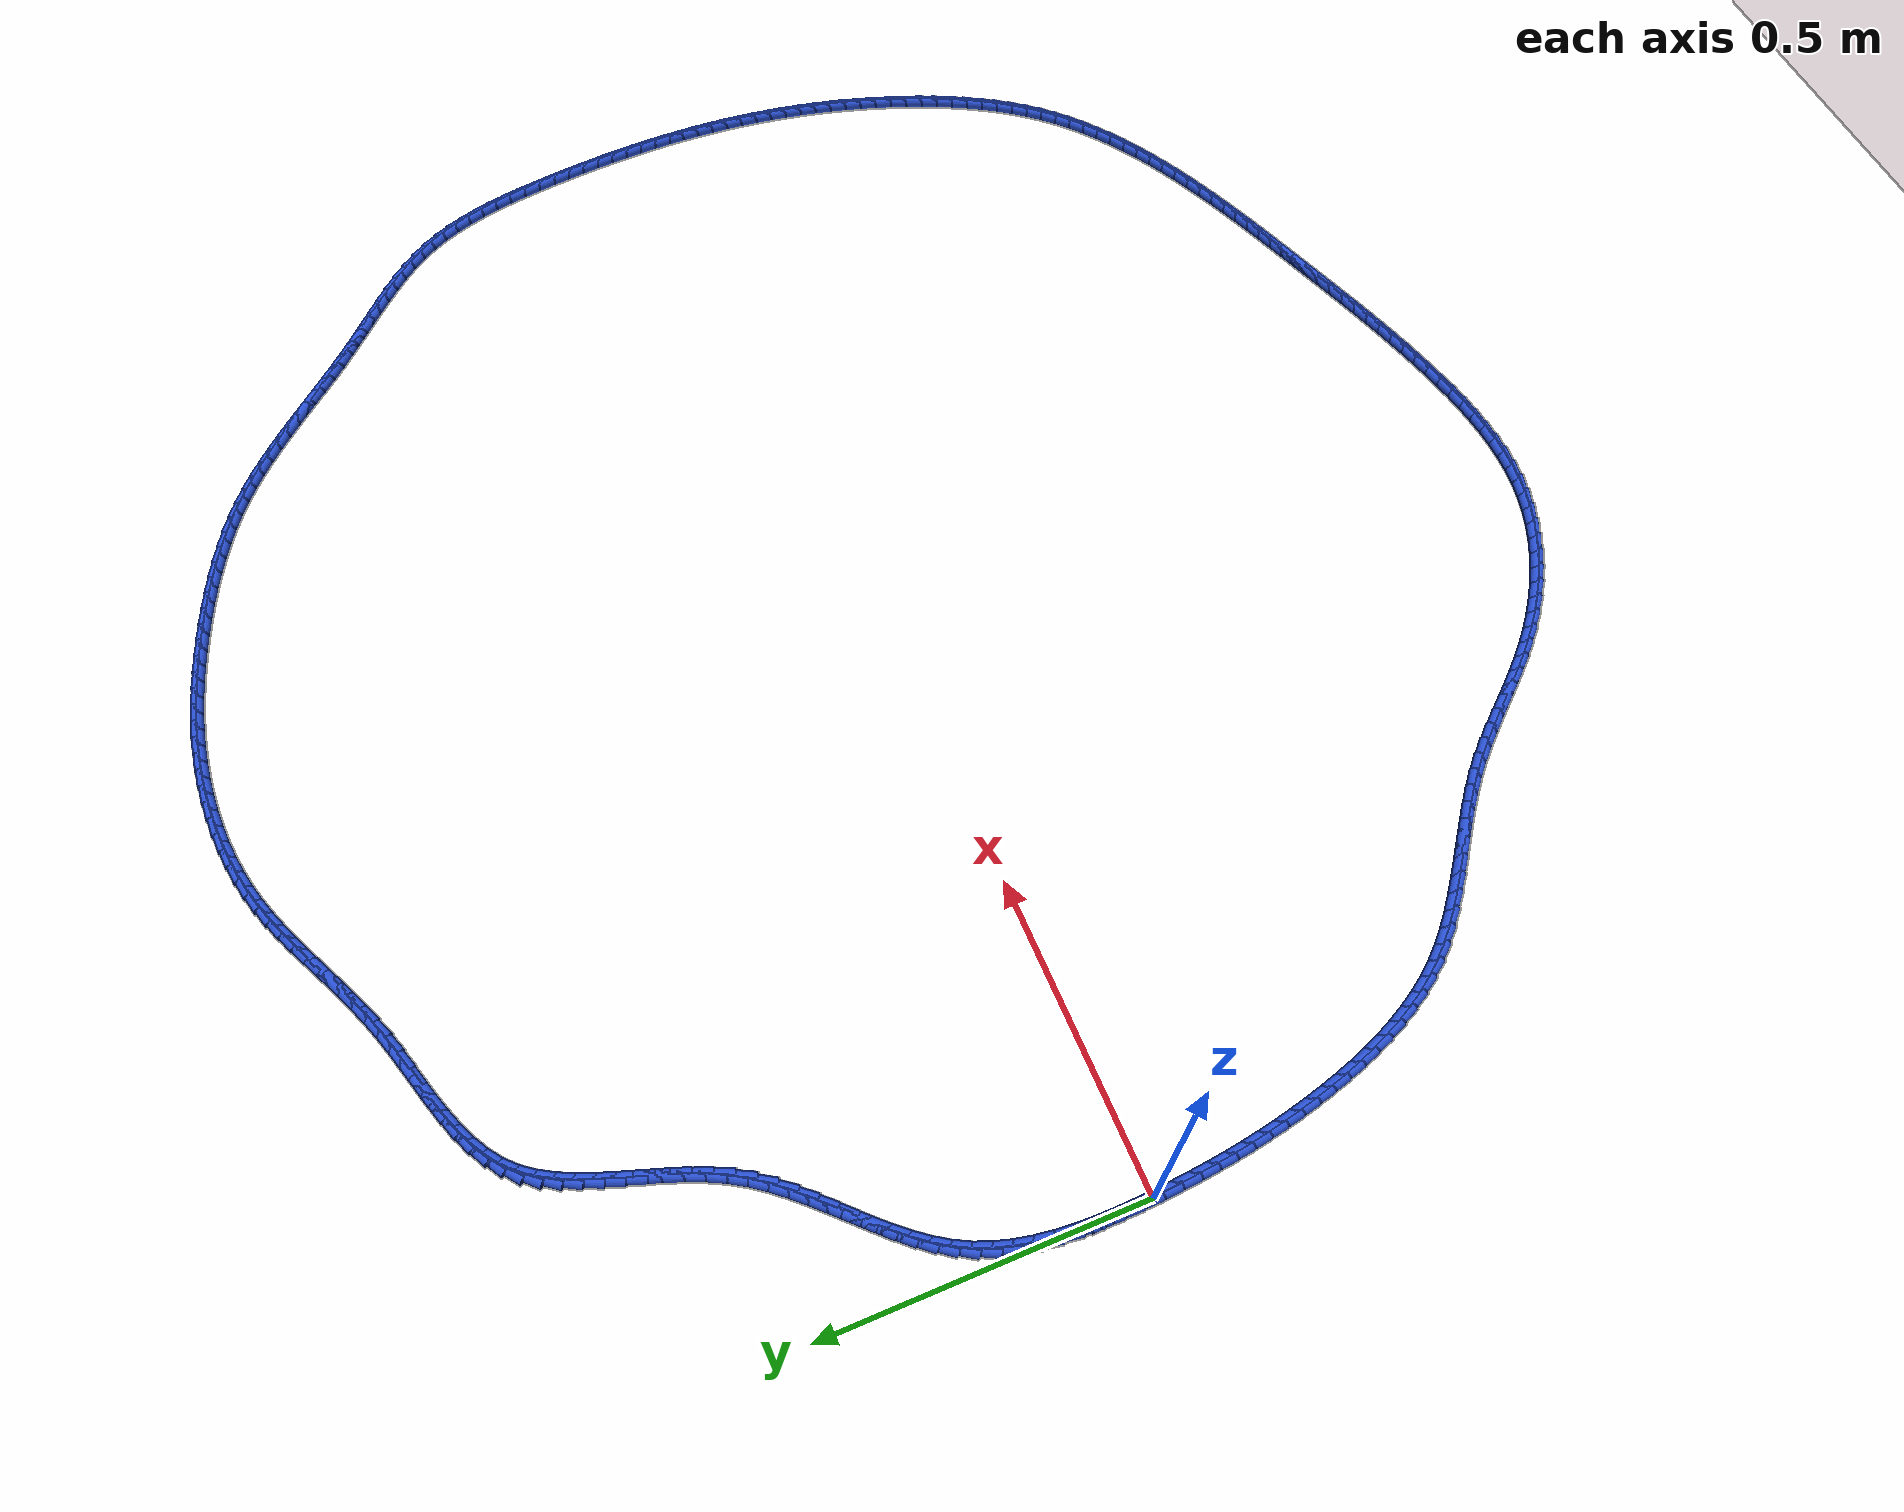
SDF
<sdf version="1.6">
 <world name="default">
  <light name="sun" type="directional">
   <pose>0 0 10 0 -0 0</pose>
   <diffuse>0.8 0.8 0.8 1</diffuse>
   <specular>0.2 0.2 0.2 1</specular>
   <attenuation>
    <range>1000</range>
    <constant>0.9</constant>
    <linear>0.01</linear>
    <quadratic>0.001</quadratic>
   </attenuation>
   <direction>-0.5 0.1 -0.9</direction>
  </light>
  <model name="ground_plane">
   <static>1</static>
   <link name="link">
    <collision name="collision">
     <geometry><plane><normal>0 0 1</normal><size>100 100</size></plane></geometry>
     <surface><friction><ode><mu>100</mu><mu2>50</mu2></ode></friction></surface>
    </collision>
    <visual name="visual">
     <cast_shadows>0</cast_shadows>
     <geometry><plane><normal>0 0 1</normal><size>100 100</size></plane></geometry>
     <material>
      <script><uri>file://media/materials/scripts/gazebo.material</uri><name>Gazebo/WhiteGlow</name></script>
     </material>
    </visual>
   </link>
  </model>
  <gravity>0 0 -9.8</gravity>
  <magnetic_field>6e-06 2.3e-05 -4.2e-05</magnetic_field>
  <atmosphere type="adiabatic"/>
  <physics name="default_physics" default="0" type="ode">
   <max_step_size>0.001</max_step_size>
   <real_time_factor>1</real_time_factor>
   <real_time_update_rate>1000</real_time_update_rate>
  </physics>
  <scene><ambient>0.4 0.4 0.4 1</ambient><background>0.7 0.7 0.7 1</background><shadows>1</shadows></scene>
  <spherical_coordinates>
   <surface_model>EARTH_WGS84</surface_model>
   <latitude_deg>0</latitude_deg>
   <longitude_deg>0</longitude_deg>
   <elevation>0</elevation>
   <heading_deg>0</heading_deg>
  </spherical_coordinates>
  <model name="line">
   <link name="link_0">
    <pose>-9.215718466126788e-18 -1.0408340855860843e-16 0.01 0 1.57 -1.529621618032261</pose>
    <collision name="collision">
     <geometry><cylinder><radius>0.01</radius><length>0.08</length></cylinder></geometry>
    </collision>
    <visual name="visual">
     <material>
      <script><name>Gazebo/Blue</name><uri>file://media/materials/scripts/gazebo.material</uri></script>
     </material>
     <geometry><cylinder><radius>0.01</radius><length>0.08</length></cylinder></geometry>
    </visual>
   </link>
   <link name="link_1">
    <pose>-0.0012172197145369874 0.02954560698774858 0.01 0 1.57 -1.5515604070414126</pose>
    <collision name="collision">
     <geometry><cylinder><radius>0.01</radius><length>0.08</length></cylinder></geometry>
    </collision>
    <visual name="visual">
     <material>
      <script><name>Gazebo/Blue</name><uri>file://media/materials/scripts/gazebo.material</uri></script>
     </material>
     <geometry><cylinder><radius>0.01</radius><length>0.08</length></cylinder></geometry>
    </visual>
   </link>
   <link name="link_2">
    <pose>-0.001789152059698116 0.05927445845407069 0.01 0 1.57 1.560852074819646</pose>
    <collision name="collision">
     <geometry><cylinder><radius>0.01</radius><length>0.08</length></cylinder></geometry>
    </collision>
    <visual name="visual">
     <material>
      <script><name>Gazebo/Blue</name><uri>file://media/materials/scripts/gazebo.material</uri></script>
     </material>
     <geometry><cylinder><radius>0.01</radius><length>0.08</length></cylinder></geometry>
    </visual>
   </link>
   <link name="link_3">
    <pose>-0.0014935204263659032 0.0890023745589933 0.01 0 1.57 1.523933544363301</pose>
    <collision name="collision">
     <geometry><cylinder><radius>0.01</radius><length>0.08</length></cylinder></geometry>
    </collision>
    <visual name="visual">
     <material>
      <script><name>Gazebo/Blue</name><uri>file://media/materials/scripts/gazebo.material</uri></script>
     </material>
     <geometry><cylinder><radius>0.01</radius><length>0.08</length></cylinder></geometry>
    </visual>
   </link>
   <link name="link_4">
    <pose>-0.00010804820542285746 0.11854517546254352 0.01 0 1.57 1.4785914215890161</pose>
    <collision name="collision">
     <geometry><cylinder><radius>0.01</radius><length>0.08</length></cylinder></geometry>
    </collision>
    <visual name="visual">
     <material>
      <script><name>Gazebo/Blue</name><uri>file://media/materials/scripts/gazebo.material</uri></script>
     </material>
     <geometry><cylinder><radius>0.01</radius><length>0.08</length></cylinder></geometry>
    </visual>
   </link>
   <link name="link_5">
    <pose>0.0025895412122485177 0.1477186813247484 0.01 0 1.57 1.4239922343526181</pose>
    <collision name="collision">
     <geometry><cylinder><radius>0.01</radius><length>0.08</length></cylinder></geometry>
    </collision>
    <visual name="visual">
     <material>
      <script><name>Gazebo/Blue</name><uri>file://media/materials/scripts/gazebo.material</uri></script>
     </material>
     <geometry><cylinder><radius>0.01</radius><length>0.08</length></cylinder></geometry>
    </visual>
   </link>
   <link name="link_6">
    <pose>0.00682152443576572 0.17633871230563505 0.01 0 1.57 1.3592278208842818</pose>
    <collision name="collision">
     <geometry><cylinder><radius>0.01</radius><length>0.08</length></cylinder></geometry>
    </collision>
    <visual name="visual">
     <material>
      <script><name>Gazebo/Blue</name><uri>file://media/materials/scripts/gazebo.material</uri></script>
     </material>
     <geometry><cylinder><radius>0.01</radius><length>0.08</length></cylinder></geometry>
    </visual>
   </link>
   <link name="link_7">
    <pose>0.012810178074246236 0.20422108856523047 0.01 0 1.57 1.2834471232154372</pose>
    <collision name="collision">
     <geometry><cylinder><radius>0.01</radius><length>0.08</length></cylinder></geometry>
    </collision>
    <visual name="visual">
     <material>
      <script><name>Gazebo/Blue</name><uri>file://media/materials/scripts/gazebo.material</uri></script>
     </material>
     <geometry><cylinder><radius>0.01</radius><length>0.08</length></cylinder></geometry>
    </visual>
   </link>
   <link name="link_8">
    <pose>0.020777778736807556 0.23118163026356178 0.01 0 1.57 1.196071126284071</pose>
    <collision name="collision">
     <geometry><cylinder><radius>0.01</radius><length>0.08</length></cylinder></geometry>
    </collision>
    <visual name="visual">
     <material>
      <script><name>Gazebo/Blue</name><uri>file://media/materials/scripts/gazebo.material</uri></script>
     </material>
     <geometry><cylinder><radius>0.01</radius><length>0.08</length></cylinder></geometry>
    </visual>
   </link>
   <link name="link_9">
    <pose>0.0309466030325672 0.2570361575606562 0.01 0 1.57 1.0976404079004878</pose>
    <collision name="collision">
     <geometry><cylinder><radius>0.01</radius><length>0.08</length></cylinder></geometry>
    </collision>
    <visual name="visual">
     <material>
      <script><name>Gazebo/Blue</name><uri>file://media/materials/scripts/gazebo.material</uri></script>
     </material>
     <geometry><cylinder><radius>0.01</radius><length>0.08</length></cylinder></geometry>
    </visual>
   </link>
   <link name="link_10">
    <pose>0.04352651727885882 0.28160906107920164 0.01 0 1.57 1.0023911948197595</pose>
    <collision name="collision">
     <geometry><cylinder><radius>0.01</radius><length>0.08</length></cylinder></geometry>
    </collision>
    <visual name="visual">
     <material>
      <script><name>Gazebo/Blue</name><uri>file://media/materials/scripts/gazebo.material</uri></script>
     </material>
     <geometry><cylinder><radius>0.01</radius><length>0.08</length></cylinder></geometry>
    </visual>
   </link>
   <link name="link_11">
    <pose>0.058424554177370344 0.3049338662664882 0.01 0 1.57 0.9254155220851544</pose>
    <collision name="collision">
     <geometry><cylinder><radius>0.01</radius><length>0.08</length></cylinder></geometry>
    </collision>
    <visual name="visual">
     <material>
      <script><name>Gazebo/Blue</name><uri>file://media/materials/scripts/gazebo.material</uri></script>
     </material>
     <geometry><cylinder><radius>0.01</radius><length>0.08</length></cylinder></geometry>
    </visual>
   </link>
   <link name="link_12">
    <pose>0.07523492046412182 0.32726013404301757 0.01 0 1.57 0.8675585224315688</pose>
    <collision name="collision">
     <geometry><cylinder><radius>0.01</radius><length>0.08</length></cylinder></geometry>
    </collision>
    <visual name="visual">
     <material>
      <script><name>Gazebo/Blue</name><uri>file://media/materials/scripts/gazebo.material</uri></script>
     </material>
     <geometry><cylinder><radius>0.01</radius><length>0.08</length></cylinder></geometry>
    </visual>
   </link>
   <link name="link_13">
    <pose>0.09353741345308561 0.348847376377646 0.01 0 1.57 0.8281887263366093</pose>
    <collision name="collision">
     <geometry><cylinder><radius>0.01</radius><length>0.08</length></cylinder></geometry>
    </collision>
    <visual name="visual">
     <material>
      <script><name>Gazebo/Blue</name><uri>file://media/materials/scripts/gazebo.material</uri></script>
     </material>
     <geometry><cylinder><radius>0.01</radius><length>0.08</length></cylinder></geometry>
    </visual>
   </link>
   <link name="link_14">
    <pose>0.11291183045823405 0.36995510523922986 0.01 0 1.57 0.8064536583959431</pose>
    <collision name="collision">
     <geometry><cylinder><radius>0.01</radius><length>0.08</length></cylinder></geometry>
    </collision>
    <visual name="visual">
     <material>
      <script><name>Gazebo/Blue</name><uri>file://media/materials/scripts/gazebo.material</uri></script>
     </material>
     <geometry><cylinder><radius>0.01</radius><length>0.08</length></cylinder></geometry>
    </visual>
   </link>
   <link name="link_15">
    <pose>0.13293796879353936 0.3908428325966253 0.01 0 1.57 0.8016546540516383</pose>
    <collision name="collision">
     <geometry><cylinder><radius>0.01</radius><length>0.08</length></cylinder></geometry>
    </collision>
    <visual name="visual">
     <material>
      <script><name>Gazebo/Blue</name><uri>file://media/materials/scripts/gazebo.material</uri></script>
     </material>
     <geometry><cylinder><radius>0.01</radius><length>0.08</length></cylinder></geometry>
    </visual>
   </link>
   <link name="link_16">
    <pose>0.15319562577297396 0.41177007041868846 0.01 0 1.57 0.8134155494075602</pose>
    <collision name="collision">
     <geometry><cylinder><radius>0.01</radius><length>0.08</length></cylinder></geometry>
    </collision>
    <visual name="visual">
     <material>
      <script><name>Gazebo/Blue</name><uri>file://media/materials/scripts/gazebo.material</uri></script>
     </material>
     <geometry><cylinder><radius>0.01</radius><length>0.08</length></cylinder></geometry>
    </visual>
   </link>
   <link name="link_17">
    <pose>0.1732645987105102 0.4329963306742757 0.01 0 1.57 0.8417021538630504</pose>
    <collision name="collision">
     <geometry><cylinder><radius>0.01</radius><length>0.08</length></cylinder></geometry>
    </collision>
    <visual name="visual">
     <material>
      <script><name>Gazebo/Blue</name><uri>file://media/materials/scripts/gazebo.material</uri></script>
     </material>
     <geometry><cylinder><radius>0.01</radius><length>0.08</length></cylinder></geometry>
    </visual>
   </link>
   <link name="link_18">
    <pose>0.19272468492012035 0.4547811253322432 0.01 0 1.57 0.8867184130049214</pose>
    <collision name="collision">
     <geometry><cylinder><radius>0.01</radius><length>0.08</length></cylinder></geometry>
    </collision>
    <visual name="visual">
     <material>
      <script><name>Gazebo/Blue</name><uri>file://media/materials/scripts/gazebo.material</uri></script>
     </material>
     <geometry><cylinder><radius>0.01</radius><length>0.08</length></cylinder></geometry>
    </visual>
   </link>
   <link name="link_19">
    <pose>0.2111556817157766 0.4773839663614469 0.01 0 1.57 0.9486721330295415</pose>
    <collision name="collision">
     <geometry><cylinder><radius>0.01</radius><length>0.08</length></cylinder></geometry>
    </collision>
    <visual name="visual">
     <material>
      <script><name>Gazebo/Blue</name><uri>file://media/materials/scripts/gazebo.material</uri></script>
     </material>
     <geometry><cylinder><radius>0.01</radius><length>0.08</length></cylinder></geometry>
    </visual>
   </link>
   <link name="link_20">
    <pose>0.22813738641145145 0.5010643657307435 0.01 0 1.57 1.0273711877691036</pose>
    <collision name="collision">
     <geometry><cylinder><radius>0.01</radius><length>0.08</length></cylinder></geometry>
    </collision>
    <visual name="visual">
     <material>
      <script><name>Gazebo/Blue</name><uri>file://media/materials/scripts/gazebo.material</uri></script>
     </material>
     <geometry><cylinder><radius>0.01</radius><length>0.08</length></cylinder></geometry>
    </visual>
   </link>
   <link name="link_21">
    <pose>0.24325009437721926 0.5260814678659033 0.01 0 1.57 1.1123333494085252</pose>
    <collision name="collision">
     <geometry><cylinder><radius>0.01</radius><length>0.08</length></cylinder></geometry>
    </collision>
    <visual name="visual">
     <material>
      <script><name>Gazebo/Blue</name><uri>file://media/materials/scripts/gazebo.material</uri></script>
     </material>
     <geometry><cylinder><radius>0.01</radius><length>0.08</length></cylinder></geometry>
    </visual>
   </link>
   <link name="link_22">
    <pose>0.25630166135879867 0.5525264878323275 0.01 0 1.57 1.1786615076906897</pose>
    <collision name="collision">
     <geometry><cylinder><radius>0.01</radius><length>0.08</length></cylinder></geometry>
    </collision>
    <visual name="visual">
     <material>
      <script><name>Gazebo/Blue</name><uri>file://media/materials/scripts/gazebo.material</uri></script>
     </material>
     <geometry><cylinder><radius>0.01</radius><length>0.08</length></cylinder></geometry>
    </visual>
   </link>
   <link name="link_23">
    <pose>0.26768711545114476 0.5800573338125545 0.01 0 1.57 1.223554133059663</pose>
    <collision name="collision">
     <geometry><cylinder><radius>0.01</radius><length>0.08</length></cylinder></geometry>
    </collision>
    <visual name="visual">
     <material>
      <script><name>Gazebo/Blue</name><uri>file://media/materials/scripts/gazebo.material</uri></script>
     </material>
     <geometry><cylinder><radius>0.01</radius><length>0.08</length></cylinder></geometry>
    </visual>
   </link>
   <link name="link_24">
    <pose>0.2778949136530935 0.6082629676445563 0.01 0 1.57 1.248135445376037</pose>
    <collision name="collision">
     <geometry><cylinder><radius>0.01</radius><length>0.08</length></cylinder></geometry>
    </collision>
    <visual name="visual">
     <material>
      <script><name>Gazebo/Blue</name><uri>file://media/materials/scripts/gazebo.material</uri></script>
     </material>
     <geometry><cylinder><radius>0.01</radius><length>0.08</length></cylinder></geometry>
    </visual>
   </link>
   <link name="link_25">
    <pose>0.28741351296348094 0.6367323511663052 0.01 0 1.57 1.252954392764001</pose>
    <collision name="collision">
     <geometry><cylinder><radius>0.01</radius><length>0.08</length></cylinder></geometry>
    </collision>
    <visual name="visual">
     <material>
      <script><name>Gazebo/Blue</name><uri>file://media/materials/scripts/gazebo.material</uri></script>
     </material>
     <geometry><cylinder><radius>0.01</radius><length>0.08</length></cylinder></geometry>
    </visual>
   </link>
   <link name="link_26">
    <pose>0.296731370381143 0.6650544462157734 0.01 0 1.57 1.2377116555474008</pose>
    <collision name="collision">
     <geometry><cylinder><radius>0.01</radius><length>0.08</length></cylinder></geometry>
    </collision>
    <visual name="visual">
     <material>
      <script><name>Gazebo/Blue</name><uri>file://media/materials/scripts/gazebo.material</uri></script>
     </material>
     <geometry><cylinder><radius>0.01</radius><length>0.08</length></cylinder></geometry>
    </visual>
   </link>
   <link name="link_27">
    <pose>0.30633694290491575 0.6928182146309326 0.01 0 1.57 1.2011473030139892</pose>
    <collision name="collision">
     <geometry><cylinder><radius>0.01</radius><length>0.08</length></cylinder></geometry>
    </collision>
    <visual name="visual">
     <material>
      <script><name>Gazebo/Blue</name><uri>file://media/materials/scripts/gazebo.material</uri></script>
     </material>
     <geometry><cylinder><radius>0.01</radius><length>0.08</length></cylinder></geometry>
    </visual>
   </link>
   <link name="link_28">
    <pose>0.31671868753363513 0.7196126182497558 0.01 0 1.57 1.141089650842048</pose>
    <collision name="collision">
     <geometry><cylinder><radius>0.01</radius><length>0.08</length></cylinder></geometry>
    </collision>
    <visual name="visual">
     <material>
      <script><name>Gazebo/Blue</name><uri>file://media/materials/scripts/gazebo.material</uri></script>
     </material>
     <geometry><cylinder><radius>0.01</radius><length>0.08</length></cylinder></geometry>
    </visual>
   </link>
   <link name="link_29">
    <pose>0.328365061266137 0.7450266189102142 0.01 0 1.57 1.0548198802588418</pose>
    <collision name="collision">
     <geometry><cylinder><radius>0.01</radius><length>0.08</length></cylinder></geometry>
    </collision>
    <visual name="visual">
     <material>
      <script><name>Gazebo/Blue</name><uri>file://media/materials/scripts/gazebo.material</uri></script>
     </material>
     <geometry><cylinder><radius>0.01</radius><length>0.08</length></cylinder></geometry>
    </visual>
   </link>
   <link name="link_30">
    <pose>0.3417645211012577 0.7686491784502809 0.01 0 1.57 0.9400862732517093</pose>
    <collision name="collision">
     <geometry><cylinder><radius>0.01</radius><length>0.08</length></cylinder></geometry>
    </collision>
    <visual name="visual">
     <material>
      <script><name>Gazebo/Blue</name><uri>file://media/materials/scripts/gazebo.material</uri></script>
     </material>
     <geometry><cylinder><radius>0.01</radius><length>0.08</length></cylinder></geometry>
    </visual>
   </link>
   <link name="link_31">
    <pose>0.357405524037833 0.7900692587079277 0.01 0 1.57 0.798821400806224</pose>
    <collision name="collision">
     <geometry><cylinder><radius>0.01</radius><length>0.08</length></cylinder></geometry>
    </collision>
    <visual name="visual">
     <material>
      <script><name>Gazebo/Blue</name><uri>file://media/materials/scripts/gazebo.material</uri></script>
     </material>
     <geometry><cylinder><radius>0.01</radius><length>0.08</length></cylinder></geometry>
    </visual>
   </link>
   <link name="link_32">
    <pose>0.3757433705107839 0.8089061403550023 0.01 0 1.57 0.6600874930666893</pose>
    <collision name="collision">
     <geometry><cylinder><radius>0.01</radius><length>0.08</length></cylinder></geometry>
    </collision>
    <visual name="visual">
     <material>
      <script><name>Gazebo/Blue</name><uri>file://media/materials/scripts/gazebo.material</uri></script>
     </material>
     <geometry><cylinder><radius>0.01</radius><length>0.08</length></cylinder></geometry>
    </visual>
   </link>
   <link name="link_33">
    <pose>0.3967551236232126 0.8252164110850838 0.01 0 1.57 0.5462867310070709</pose>
    <collision name="collision">
     <geometry><cylinder><radius>0.01</radius><length>0.08</length></cylinder></geometry>
    </collision>
    <visual name="visual">
     <material>
      <script><name>Gazebo/Blue</name><uri>file://media/materials/scripts/gazebo.material</uri></script>
     </material>
     <geometry><cylinder><radius>0.01</radius><length>0.08</length></cylinder></geometry>
    </visual>
   </link>
   <link name="link_34">
    <pose>0.4200586355763249 0.8393851261521664 0.01 0 1.57 0.457854576641668</pose>
    <collision name="collision">
     <geometry><cylinder><radius>0.01</radius><length>0.08</length></cylinder></geometry>
    </collision>
    <visual name="visual">
     <material>
      <script><name>Gazebo/Blue</name><uri>file://media/materials/scripts/gazebo.material</uri></script>
     </material>
     <geometry><cylinder><radius>0.01</radius><length>0.08</length></cylinder></geometry>
    </visual>
   </link>
   <link name="link_35">
    <pose>0.4452630202099234 0.8518053312922619 0.01 0 1.57 0.3926762718178306</pose>
    <collision name="collision">
     <geometry><cylinder><radius>0.01</radius><length>0.08</length></cylinder></geometry>
    </collision>
    <visual name="visual">
     <material>
      <script><name>Gazebo/Blue</name><uri>file://media/materials/scripts/gazebo.material</uri></script>
     </material>
     <geometry><cylinder><radius>0.01</radius><length>0.08</length></cylinder></geometry>
    </visual>
   </link>
   <link name="link_36">
    <pose>0.47197739136381084 0.8628700722413811 0.01 0 1.57 0.34816987220878004</pose>
    <collision name="collision">
     <geometry><cylinder><radius>0.01</radius><length>0.08</length></cylinder></geometry>
    </collision>
    <visual name="visual">
     <material>
      <script><name>Gazebo/Blue</name><uri>file://media/materials/scripts/gazebo.material</uri></script>
     </material>
     <geometry><cylinder><radius>0.01</radius><length>0.08</length></cylinder></geometry>
    </visual>
   </link>
   <link name="link_37">
    <pose>0.49981086287779014 0.8729723947355363 0.01 0 1.57 0.3221408546250163</pose>
    <collision name="collision">
     <geometry><cylinder><radius>0.01</radius><length>0.08</length></cylinder></geometry>
    </collision>
    <visual name="visual">
     <material>
      <script><name>Gazebo/Blue</name><uri>file://media/materials/scripts/gazebo.material</uri></script>
     </material>
     <geometry><cylinder><radius>0.01</radius><length>0.08</length></cylinder></geometry>
    </visual>
   </link>
   <link name="link_38">
    <pose>0.5283725485916635 0.8825053445107381 0.01 0 1.57 0.31311866313273773</pose>
    <collision name="collision">
     <geometry><cylinder><radius>0.01</radius><length>0.08</length></cylinder></geometry>
    </collision>
    <visual name="visual">
     <material>
      <script><name>Gazebo/Blue</name><uri>file://media/materials/scripts/gazebo.material</uri></script>
     </material>
     <geometry><cylinder><radius>0.01</radius><length>0.08</length></cylinder></geometry>
    </visual>
   </link>
   <link name="link_39">
    <pose>0.5572715623452341 0.8918619673029986 0.01 0 1.57 0.32044547369359994</pose>
    <collision name="collision">
     <geometry><cylinder><radius>0.01</radius><length>0.08</length></cylinder></geometry>
    </collision>
    <visual name="visual">
     <material>
      <script><name>Gazebo/Blue</name><uri>file://media/materials/scripts/gazebo.material</uri></script>
     </material>
     <geometry><cylinder><radius>0.01</radius><length>0.08</length></cylinder></geometry>
    </visual>
   </link>
   <link name="link_40">
    <pose>0.5861170179783048 0.9014353088483292 0.01 0 1.57 0.3442689581863764</pose>
    <collision name="collision">
     <geometry><cylinder><radius>0.01</radius><length>0.08</length></cylinder></geometry>
    </collision>
    <visual name="visual">
     <material>
      <script><name>Gazebo/Blue</name><uri>file://media/materials/scripts/gazebo.material</uri></script>
     </material>
     <geometry><cylinder><radius>0.01</radius><length>0.08</length></cylinder></geometry>
    </visual>
   </link>
   <link name="link_41">
    <pose>0.614518029330678 0.9116184148827412 0.01 0 1.57 0.3823207800764442</pose>
    <collision name="collision">
     <geometry><cylinder><radius>0.01</radius><length>0.08</length></cylinder></geometry>
    </collision>
    <visual name="visual">
     <material>
      <script><name>Gazebo/Blue</name><uri>file://media/materials/scripts/gazebo.material</uri></script>
     </material>
     <geometry><cylinder><radius>0.01</radius><length>0.08</length></cylinder></geometry>
    </visual>
   </link>
   <link name="link_42">
    <pose>0.6421481441470507 0.922728656417441 0.01 0 1.57 0.4178861468979338</pose>
    <collision name="collision">
     <geometry><cylinder><radius>0.01</radius><length>0.08</length></cylinder></geometry>
    </collision>
    <visual name="visual">
     <material>
      <script><name>Gazebo/Blue</name><uri>file://media/materials/scripts/gazebo.material</uri></script>
     </material>
     <geometry><cylinder><radius>0.01</radius><length>0.08</length></cylinder></geometry>
    </visual>
   </link>
   <link name="link_43">
    <pose>0.6690350363696759 0.9346674991636218 0.01 0 1.57 0.4446240596285598</pose>
    <collision name="collision">
     <geometry><cylinder><radius>0.01</radius><length>0.08</length></cylinder></geometry>
    </collision>
    <visual name="visual">
     <material>
      <script><name>Gazebo/Blue</name><uri>file://media/materials/scripts/gazebo.material</uri></script>
     </material>
     <geometry><cylinder><radius>0.01</radius><length>0.08</length></cylinder></geometry>
    </visual>
   </link>
   <link name="link_44">
    <pose>0.6953273975483508 0.9471942790925119 0.01 0 1.57 0.4621179388728625</pose>
    <collision name="collision">
     <geometry><cylinder><radius>0.01</radius><length>0.08</length></cylinder></geometry>
    </collision>
    <visual name="visual">
     <material>
      <script><name>Gazebo/Blue</name><uri>file://media/materials/scripts/gazebo.material</uri></script>
     </material>
     <geometry><cylinder><radius>0.01</radius><length>0.08</length></cylinder></geometry>
    </visual>
   </link>
   <link name="link_45">
    <pose>0.7211740240577932 0.9600682090631836 0.01 0 1.57 0.47005981276297243</pose>
    <collision name="collision">
     <geometry><cylinder><radius>0.01</radius><length>0.08</length></cylinder></geometry>
    </collision>
    <visual name="visual">
     <material>
      <script><name>Gazebo/Blue</name><uri>file://media/materials/scripts/gazebo.material</uri></script>
     </material>
     <geometry><cylinder><radius>0.01</radius><length>0.08</length></cylinder></geometry>
    </visual>
   </link>
   <link name="link_46">
    <pose>0.7467237122727204 0.9730485019347095 0.01 0 1.57 0.46820681863325114</pose>
    <collision name="collision">
     <geometry><cylinder><radius>0.01</radius><length>0.08</length></cylinder></geometry>
    </collision>
    <visual name="visual">
     <material>
      <script><name>Gazebo/Blue</name><uri>file://media/materials/scripts/gazebo.material</uri></script>
     </material>
     <geometry><cylinder><radius>0.01</radius><length>0.08</length></cylinder></geometry>
    </visual>
   </link>
   <link name="link_47">
    <pose>0.7721252585678502 0.9858943705661616 0.01 0 1.57 0.45636388445263176</pose>
    <collision name="collision">
     <geometry><cylinder><radius>0.01</radius><length>0.08</length></cylinder></geometry>
    </collision>
    <visual name="visual">
     <material>
      <script><name>Gazebo/Blue</name><uri>file://media/materials/scripts/gazebo.material</uri></script>
     </material>
     <geometry><cylinder><radius>0.01</radius><length>0.08</length></cylinder></geometry>
    </visual>
   </link>
   <link name="link_48">
    <pose>0.7975274593179 0.9983650278166122 0.01 0 1.57 0.4343930324177372</pose>
    <collision name="collision">
     <geometry><cylinder><radius>0.01</radius><length>0.08</length></cylinder></geometry>
    </collision>
    <visual name="visual">
     <material>
      <script><name>Gazebo/Blue</name><uri>file://media/materials/scripts/gazebo.material</uri></script>
     </material>
     <geometry><cylinder><radius>0.01</radius><length>0.08</length></cylinder></geometry>
    </visual>
   </link>
   <link name="link_49">
    <pose>0.8230791108975867 1.0102196865451334 0.01 0 1.57 0.4022528412503165</pose>
    <collision name="collision">
     <geometry><cylinder><radius>0.01</radius><length>0.08</length></cylinder></geometry>
    </collision>
    <visual name="visual">
     <material>
      <script><name>Gazebo/Blue</name><uri>file://media/materials/scripts/gazebo.material</uri></script>
     </material>
     <geometry><cylinder><radius>0.01</radius><length>0.08</length></cylinder></geometry>
    </visual>
   </link>
   <link name="link_50">
    <pose>0.8489290096816288 1.0212175596107982 0.01 0 1.57 0.36006848537966896</pose>
    <collision name="collision">
     <geometry><cylinder><radius>0.01</radius><length>0.08</length></cylinder></geometry>
    </collision>
    <visual name="visual">
     <material>
      <script><name>Gazebo/Blue</name><uri>file://media/materials/scripts/gazebo.material</uri></script>
     </material>
     <geometry><cylinder><radius>0.01</radius><length>0.08</length></cylinder></geometry>
    </visual>
   </link>
   <link name="link_51">
    <pose>0.8752259520447435 1.0311178598726787 0.01 0 1.57 0.308358683951381</pose>
    <collision name="collision">
     <geometry><cylinder><radius>0.01</radius><length>0.08</length></cylinder></geometry>
    </collision>
    <visual name="visual">
     <material>
      <script><name>Gazebo/Blue</name><uri>file://media/materials/scripts/gazebo.material</uri></script>
     </material>
     <geometry><cylinder><radius>0.01</radius><length>0.08</length></cylinder></geometry>
    </visual>
   </link>
   <link name="link_52">
    <pose>0.9021159305384733 1.0396828214953764 0.01 0 1.57 0.25281044482680665</pose>
    <collision name="collision">
     <geometry><cylinder><radius>0.01</radius><length>0.08</length></cylinder></geometry>
    </collision>
    <visual name="visual">
     <material>
      <script><name>Gazebo/Blue</name><uri>file://media/materials/scripts/gazebo.material</uri></script>
     </material>
     <geometry><cylinder><radius>0.01</radius><length>0.08</length></cylinder></geometry>
    </visual>
   </link>
   <link name="link_53">
    <pose>0.9296358290076907 1.0467922505152725 0.01 0 1.57 0.20005198882270578</pose>
    <collision name="collision">
     <geometry><cylinder><radius>0.01</radius><length>0.08</length></cylinder></geometry>
    </collision>
    <visual name="visual">
     <material>
      <script><name>Gazebo/Blue</name><uri>file://media/materials/scripts/gazebo.material</uri></script>
     </material>
     <geometry><cylinder><radius>0.01</radius><length>0.08</length></cylinder></geometry>
    </visual>
   </link>
   <link name="link_54">
    <pose>0.9576807315118115 1.0524787516472653 0.01 0 1.57 0.15019814692973144</pose>
    <collision name="collision">
     <geometry><cylinder><radius>0.01</radius><length>0.08</length></cylinder></geometry>
    </collision>
    <visual name="visual">
     <material>
      <script><name>Gazebo/Blue</name><uri>file://media/materials/scripts/gazebo.material</uri></script>
     </material>
     <geometry><cylinder><radius>0.01</radius><length>0.08</length></cylinder></geometry>
    </visual>
   </link>
   <link name="link_55">
    <pose>0.9861362389798977 1.0567851483085005 0.01 0 1.57 0.10290267627874924</pose>
    <collision name="collision">
     <geometry><cylinder><radius>0.01</radius><length>0.08</length></cylinder></geometry>
    </collision>
    <visual name="visual">
     <material>
      <script><name>Gazebo/Blue</name><uri>file://media/materials/scripts/gazebo.material</uri></script>
     </material>
     <geometry><cylinder><radius>0.01</radius><length>0.08</length></cylinder></geometry>
    </visual>
   </link>
   <link name="link_56">
    <pose>1.0148879523410097 1.0597542639161242 0.01 0 1.57 0.0578150067700696</pose>
    <collision name="collision">
     <geometry><cylinder><radius>0.01</radius><length>0.08</length></cylinder></geometry>
    </collision>
    <visual name="visual">
     <material>
      <script><name>Gazebo/Blue</name><uri>file://media/materials/scripts/gazebo.material</uri></script>
     </material>
     <geometry><cylinder><radius>0.01</radius><length>0.08</length></cylinder></geometry>
    </visual>
   </link>
   <link name="link_57">
    <pose>1.043821472524209 1.0614289218872823 0.01 0 1.57 0.014585524804405633</pose>
    <collision name="collision">
     <geometry><cylinder><radius>0.01</radius><length>0.08</length></cylinder></geometry>
    </collision>
    <visual name="visual">
     <material>
      <script><name>Gazebo/Blue</name><uri>file://media/materials/scripts/gazebo.material</uri></script>
     </material>
     <geometry><cylinder><radius>0.01</radius><length>0.08</length></cylinder></geometry>
    </visual>
   </link>
   <link name="link_58">
    <pose>1.0728224004585563 1.0618519456391216 0.01 0 1.57 -0.027132552841534034</pose>
    <collision name="collision">
     <geometry><cylinder><radius>0.01</radius><length>0.08</length></cylinder></geometry>
    </collision>
    <visual name="visual">
     <material>
      <script><name>Gazebo/Blue</name><uri>file://media/materials/scripts/gazebo.material</uri></script>
     </material>
     <geometry><cylinder><radius>0.01</radius><length>0.08</length></cylinder></geometry>
    </visual>
   </link>
   <link name="link_59">
    <pose>1.101776337073114 1.0610661585887875 0.01 0 1.57 -0.06766742960515118</pose>
    <collision name="collision">
     <geometry><cylinder><radius>0.01</radius><length>0.08</length></cylinder></geometry>
    </collision>
    <visual name="visual">
     <material>
      <script><name>Gazebo/Blue</name><uri>file://media/materials/scripts/gazebo.material</uri></script>
     </material>
     <geometry><cylinder><radius>0.01</radius><length>0.08</length></cylinder></geometry>
    </visual>
   </link>
   <link name="link_60">
    <pose>1.1305710996707277 1.0591147116269546 0.01 0 1.57 -0.10684642102839555</pose>
    <collision name="collision">
     <geometry><cylinder><radius>0.01</radius><length>0.08</length></cylinder></geometry>
    </collision>
    <visual name="visual">
     <material>
      <script><name>Gazebo/Blue</name><uri>file://media/materials/scripts/gazebo.material</uri></script>
     </material>
     <geometry><cylinder><radius>0.01</radius><length>0.08</length></cylinder></geometry>
    </visual>
   </link>
   <link name="link_61">
    <pose>1.159152078755189 1.0560492621964712 0.01 0 1.57 -0.14415059331320842</pose>
    <collision name="collision">
     <geometry><cylinder><radius>0.01</radius><length>0.08</length></cylinder></geometry>
    </collision>
    <visual name="visual">
     <material>
      <script><name>Gazebo/Blue</name><uri>file://media/materials/scripts/gazebo.material</uri></script>
     </material>
     <geometry><cylinder><radius>0.01</radius><length>0.08</length></cylinder></geometry>
    </visual>
   </link>
   <link name="link_62">
    <pose>1.1875261603216454 1.0519305538183812 0.01 0 1.57 -0.17943009595995915</pose>
    <collision name="collision">
     <geometry><cylinder><radius>0.01</radius><length>0.08</length></cylinder></geometry>
    </collision>
    <visual name="visual">
     <material>
      <script><name>Gazebo/Blue</name><uri>file://media/materials/scripts/gazebo.material</uri></script>
     </material>
     <geometry><cylinder><radius>0.01</radius><length>0.08</length></cylinder></geometry>
    </visual>
   </link>
   <link name="link_63">
    <pose>1.2157032322654355 1.0468197735503064 0.01 0 1.57 -0.21258963515773768</pose>
    <collision name="collision">
     <geometry><cylinder><radius>0.01</radius><length>0.08</length></cylinder></geometry>
    </collision>
    <visual name="visual">
     <material>
      <script><name>Gazebo/Blue</name><uri>file://media/materials/scripts/gazebo.material</uri></script>
     </material>
     <geometry><cylinder><radius>0.01</radius><length>0.08</length></cylinder></geometry>
    </visual>
   </link>
   <link name="link_64">
    <pose>1.2436931824818966 1.040778108449869 0.01 0 1.57 -0.24356311118365087</pose>
    <collision name="collision">
     <geometry><cylinder><radius>0.01</radius><length>0.08</length></cylinder></geometry>
    </collision>
    <visual name="visual">
     <material>
      <script><name>Gazebo/Blue</name><uri>file://media/materials/scripts/gazebo.material</uri></script>
     </material>
     <geometry><cylinder><radius>0.01</radius><length>0.08</length></cylinder></geometry>
    </visual>
   </link>
   <link name="link_65">
    <pose>1.2715058988663672 1.0338667455746928 0.01 0 1.57 -0.2723098680784848</pose>
    <collision name="collision">
     <geometry><cylinder><radius>0.01</radius><length>0.08</length></cylinder></geometry>
    </collision>
    <visual name="visual">
     <material>
      <script><name>Gazebo/Blue</name><uri>file://media/materials/scripts/gazebo.material</uri></script>
     </material>
     <geometry><cylinder><radius>0.01</radius><length>0.08</length></cylinder></geometry>
    </visual>
   </link>
   <link name="link_66">
    <pose>1.2991512693141847 1.0261468719823983 0.01 0 1.57 -0.29881056505418174</pose>
    <collision name="collision">
     <geometry><cylinder><radius>0.01</radius><length>0.08</length></cylinder></geometry>
    </collision>
    <visual name="visual">
     <material>
      <script><name>Gazebo/Blue</name><uri>file://media/materials/scripts/gazebo.material</uri></script>
     </material>
     <geometry><cylinder><radius>0.01</radius><length>0.08</length></cylinder></geometry>
    </visual>
   </link>
   <link name="link_67">
    <pose>1.3266391817206868 1.0176796747306092 0.01 0 1.57 -0.323062976342067</pose>
    <collision name="collision">
     <geometry><cylinder><radius>0.01</radius><length>0.08</length></cylinder></geometry>
    </collision>
    <visual name="visual">
     <material>
      <script><name>Gazebo/Blue</name><uri>file://media/materials/scripts/gazebo.material</uri></script>
     </material>
     <geometry><cylinder><radius>0.01</radius><length>0.08</length></cylinder></geometry>
    </visual>
   </link>
   <link name="link_68">
    <pose>1.353979523981212 1.0085263408769474 0.01 0 1.57 -0.3454287903798433</pose>
    <collision name="collision">
     <geometry><cylinder><radius>0.01</radius><length>0.08</length></cylinder></geometry>
    </collision>
    <visual name="visual">
     <material>
      <script><name>Gazebo/Blue</name><uri>file://media/materials/scripts/gazebo.material</uri></script>
     </material>
     <geometry><cylinder><radius>0.01</radius><length>0.08</length></cylinder></geometry>
    </visual>
   </link>
   <link name="link_69">
    <pose>1.3811750822521391 0.99873983472967 0.01 0 1.57 -0.3689026181443</pose>
    <collision name="collision">
     <geometry><cylinder><radius>0.01</radius><length>0.08</length></cylinder></geometry>
    </collision>
    <visual name="visual">
     <material>
      <script><name>Gazebo/Blue</name><uri>file://media/materials/scripts/gazebo.material</uri></script>
     </material>
     <geometry><cylinder><radius>0.01</radius><length>0.08</length></cylinder></geometry>
    </visual>
   </link>
   <link name="link_70">
    <pose>1.408168928557708 0.9883039805814691 0.01 0 1.57 -0.3950704069448111</pose>
    <collision name="collision">
     <geometry><cylinder><radius>0.01</radius><length>0.08</length></cylinder></geometry>
    </collision>
    <visual name="visual">
     <material>
      <script><name>Gazebo/Blue</name><uri>file://media/materials/scripts/gazebo.material</uri></script>
     </material>
     <geometry><cylinder><radius>0.01</radius><length>0.08</length></cylinder></geometry>
    </visual>
   </link>
   <link name="link_71">
    <pose>1.4348742554001352 0.9771680067166257 0.01 0 1.57 -0.4240762697669209</pose>
    <collision name="collision">
     <geometry><cylinder><radius>0.01</radius><length>0.08</length></cylinder></geometry>
    </collision>
    <visual name="visual">
     <material>
      <script><name>Gazebo/Blue</name><uri>file://media/materials/scripts/gazebo.material</uri></script>
     </material>
     <geometry><cylinder><radius>0.01</radius><length>0.08</length></cylinder></geometry>
    </visual>
   </link>
   <link name="link_72">
    <pose>1.4612040330769993 0.9652808841397503 0.01 0 1.57 -0.4560636160199288</pose>
    <collision name="collision">
     <geometry><cylinder><radius>0.01</radius><length>0.08</length></cylinder></geometry>
    </collision>
    <visual name="visual">
     <material>
      <script><name>Gazebo/Blue</name><uri>file://media/materials/scripts/gazebo.material</uri></script>
     </material>
     <geometry><cylinder><radius>0.01</radius><length>0.08</length></cylinder></geometry>
    </visual>
   </link>
   <link name="link_73">
    <pose>1.4870712318858776 0.9525915838554548 0.01 0 1.57 -0.49118018595574087</pose>
    <collision name="collision">
     <geometry><cylinder><radius>0.01</radius><length>0.08</length></cylinder></geometry>
    </collision>
    <visual name="visual">
     <material>
      <script><name>Gazebo/Blue</name><uri>file://media/materials/scripts/gazebo.material</uri></script>
     </material>
     <geometry><cylinder><radius>0.01</radius><length>0.08</length></cylinder></geometry>
    </visual>
   </link>
   <link name="link_74">
    <pose>1.5123888221243484 0.9390490768683495 0.01 0 1.57 -0.5295701697491372</pose>
    <collision name="collision">
     <geometry><cylinder><radius>0.01</radius><length>0.08</length></cylinder></geometry>
    </collision>
    <visual name="visual">
     <material>
      <script><name>Gazebo/Blue</name><uri>file://media/materials/scripts/gazebo.material</uri></script>
     </material>
     <geometry><cylinder><radius>0.01</radius><length>0.08</length></cylinder></geometry>
    </visual>
   </link>
   <link name="link_75">
    <pose>1.537069774089989 0.9246023341830459 0.01 0 1.57 -0.5713639500033487</pose>
    <collision name="collision">
     <geometry><cylinder><radius>0.01</radius><length>0.08</length></cylinder></geometry>
    </collision>
    <visual name="visual">
     <material>
      <script><name>Gazebo/Blue</name><uri>file://media/materials/scripts/gazebo.material</uri></script>
     </material>
     <geometry><cylinder><radius>0.01</radius><length>0.08</length></cylinder></geometry>
    </visual>
   </link>
   <link name="link_76">
    <pose>1.5610270580803776 0.9092003268041552 0.01 0 1.57 -0.6166651408946562</pose>
    <collision name="collision">
     <geometry><cylinder><radius>0.01</radius><length>0.08</length></cylinder></geometry>
    </collision>
    <visual name="visual">
     <material>
      <script><name>Gazebo/Blue</name><uri>file://media/materials/scripts/gazebo.material</uri></script>
     </material>
     <geometry><cylinder><radius>0.01</radius><length>0.08</length></cylinder></geometry>
    </visual>
   </link>
   <link name="link_77">
    <pose>1.584173644594408 0.892792025906398 0.01 0 1.57 -0.6638667803113913</pose>
    <collision name="collision">
     <geometry><cylinder><radius>0.01</radius><length>0.08</length></cylinder></geometry>
    </collision>
    <visual name="visual">
     <material>
      <script><name>Gazebo/Blue</name><uri>file://media/materials/scripts/gazebo.material</uri></script>
     </material>
     <geometry><cylinder><radius>0.01</radius><length>0.08</length></cylinder></geometry>
    </visual>
   </link>
   <link name="link_78">
    <pose>1.6064593175523676 0.8753575096886861 0.01 0 1.57 -0.7065350555855462</pose>
    <collision name="collision">
     <geometry><cylinder><radius>0.01</radius><length>0.08</length></cylinder></geometry>
    </collision>
    <visual name="visual">
     <material>
      <script><name>Gazebo/Blue</name><uri>file://media/materials/scripts/gazebo.material</uri></script>
     </material>
     <geometry><cylinder><radius>0.01</radius><length>0.08</length></cylinder></geometry>
    </visual>
   </link>
   <link name="link_79">
    <pose>1.6279734042852283 0.8569947693307737 0.01 0 1.57 -0.7429592636408965</pose>
    <collision name="collision">
     <geometry><cylinder><radius>0.01</radius><length>0.08</length></cylinder></geometry>
    </collision>
    <visual name="visual">
     <material>
      <script><name>Gazebo/Blue</name><uri>file://media/materials/scripts/gazebo.material</uri></script>
     </material>
     <geometry><cylinder><radius>0.01</radius><length>0.08</length></cylinder></geometry>
    </visual>
   </link>
   <link name="link_80">
    <pose>1.64883829032963 0.8378297299116434 0.01 0 1.57 -0.7730378206280935</pose>
    <collision name="collision">
     <geometry><cylinder><radius>0.01</radius><length>0.08</length></cylinder></geometry>
    </collision>
    <visual name="visual">
     <material>
      <script><name>Gazebo/Blue</name><uri>file://media/materials/scripts/gazebo.material</uri></script>
     </material>
     <geometry><cylinder><radius>0.01</radius><length>0.08</length></cylinder></geometry>
    </visual>
   </link>
   <link name="link_81">
    <pose>1.6691763612222144 0.8179883165102773 0.01 0 1.57 -0.7967607321528472</pose>
    <collision name="collision">
     <geometry><cylinder><radius>0.01</radius><length>0.08</length></cylinder></geometry>
    </collision>
    <visual name="visual">
     <material>
      <script><name>Gazebo/Blue</name><uri>file://media/materials/scripts/gazebo.material</uri></script>
     </material>
     <geometry><cylinder><radius>0.01</radius><length>0.08</length></cylinder></geometry>
    </visual>
   </link>
   <link name="link_82">
    <pose>1.6891100024996213 0.7975964542056584 0.01 0 1.57 -0.8141731932817932</pose>
    <collision name="collision">
     <geometry><cylinder><radius>0.01</radius><length>0.08</length></cylinder></geometry>
    </collision>
    <visual name="visual">
     <material>
      <script><name>Gazebo/Blue</name><uri>file://media/materials/scripts/gazebo.material</uri></script>
     </material>
     <geometry><cylinder><radius>0.01</radius><length>0.08</length></cylinder></geometry>
    </visual>
   </link>
   <link name="link_83">
    <pose>1.7087615996984935 0.7767800680767682 0.01 0 1.57 -0.8253465906681683</pose>
    <collision name="collision">
     <geometry><cylinder><radius>0.01</radius><length>0.08</length></cylinder></geometry>
    </collision>
    <visual name="visual">
     <material>
      <script><name>Gazebo/Blue</name><uri>file://media/materials/scripts/gazebo.material</uri></script>
     </material>
     <geometry><cylinder><radius>0.01</radius><length>0.08</length></cylinder></geometry>
    </visual>
   </link>
   <link name="link_84">
    <pose>1.7282535383554707 0.7556650832025902 0.01 0 1.57 -0.8303577406982188</pose>
    <collision name="collision">
     <geometry><cylinder><radius>0.01</radius><length>0.08</length></cylinder></geometry>
    </collision>
    <visual name="visual">
     <material>
      <script><name>Gazebo/Blue</name><uri>file://media/materials/scripts/gazebo.material</uri></script>
     </material>
     <geometry><cylinder><radius>0.01</radius><length>0.08</length></cylinder></geometry>
    </visual>
   </link>
   <link name="link_85">
    <pose>1.7477082040071952 0.7343774246621062 0.01 0 1.57 -0.8292761529731304</pose>
    <collision name="collision">
     <geometry><cylinder><radius>0.01</radius><length>0.08</length></cylinder></geometry>
    </collision>
    <visual name="visual">
     <material>
      <script><name>Gazebo/Blue</name><uri>file://media/materials/scripts/gazebo.material</uri></script>
     </material>
     <geometry><cylinder><radius>0.01</radius><length>0.08</length></cylinder></geometry>
    </visual>
   </link>
   <link name="link_86">
    <pose>1.7672479821903062 0.713043017534299 0.01 0 1.57 -0.8221587223452365</pose>
    <collision name="collision">
     <geometry><cylinder><radius>0.01</radius><length>0.08</length></cylinder></geometry>
    </collision>
    <visual name="visual">
     <material>
      <script><name>Gazebo/Blue</name><uri>file://media/materials/scripts/gazebo.material</uri></script>
     </material>
     <geometry><cylinder><radius>0.01</radius><length>0.08</length></cylinder></geometry>
    </visual>
   </link>
   <link name="link_87">
    <pose>1.7869952584414461 0.6917877868981508 0.01 0 1.57 -0.8090512603980048</pose>
    <collision name="collision">
     <geometry><cylinder><radius>0.01</radius><length>0.08</length></cylinder></geometry>
    </collision>
    <visual name="visual">
     <material>
      <script><name>Gazebo/Blue</name><uri>file://media/materials/scripts/gazebo.material</uri></script>
     </material>
     <geometry><cylinder><radius>0.01</radius><length>0.08</length></cylinder></geometry>
    </visual>
   </link>
   <link name="link_88">
    <pose>1.8070724182972562 0.670737657832644 0.01 0 1.57 -0.7901969047849586</pose>
    <collision name="collision">
     <geometry><cylinder><radius>0.01</radius><length>0.08</length></cylinder></geometry>
    </collision>
    <visual name="visual">
     <material>
      <script><name>Gazebo/Blue</name><uri>file://media/materials/scripts/gazebo.material</uri></script>
     </material>
     <geometry><cylinder><radius>0.01</radius><length>0.08</length></cylinder></geometry>
    </visual>
   </link>
   <link name="link_89">
    <pose>1.827597165876979 0.6500149729723794 0.01 0 1.57 -0.7725561242631066</pose>
    <collision name="collision">
     <geometry><cylinder><radius>0.01</radius><length>0.08</length></cylinder></geometry>
    </collision>
    <visual name="visual">
     <material>
      <script><name>Gazebo/Blue</name><uri>file://media/materials/scripts/gazebo.material</uri></script>
     </material>
     <geometry><cylinder><radius>0.01</radius><length>0.08</length></cylinder></geometry>
    </visual>
   </link>
   <link name="link_90">
    <pose>1.8485249522106777 0.6296179111318113 0.01 0 1.57 -0.7645857672469221</pose>
    <collision name="collision">
     <geometry><cylinder><radius>0.01</radius><length>0.08</length></cylinder></geometry>
    </collision>
    <visual name="visual">
     <material>
      <script><name>Gazebo/Blue</name><uri>file://media/materials/scripts/gazebo.material</uri></script>
     </material>
     <geometry><cylinder><radius>0.01</radius><length>0.08</length></cylinder></geometry>
    </visual>
   </link>
   <link name="link_91">
    <pose>1.8696112121468993 0.6093915891817782 0.01 0 1.57 -0.766764891529967</pose>
    <collision name="collision">
     <geometry><cylinder><radius>0.01</radius><length>0.08</length></cylinder></geometry>
    </collision>
    <visual name="visual">
     <material>
      <script><name>Gazebo/Blue</name><uri>file://media/materials/scripts/gazebo.material</uri></script>
     </material>
     <geometry><cylinder><radius>0.01</radius><length>0.08</length></cylinder></geometry>
    </visual>
   </link>
   <link name="link_92">
    <pose>1.8905990426905155 0.5891716824853415 0.01 0 1.57 -0.7791880475556096</pose>
    <collision name="collision">
     <geometry><cylinder><radius>0.01</radius><length>0.08</length></cylinder></geometry>
    </collision>
    <visual name="visual">
     <material>
      <script><name>Gazebo/Blue</name><uri>file://media/materials/scripts/gazebo.material</uri></script>
     </material>
     <geometry><cylinder><radius>0.01</radius><length>0.08</length></cylinder></geometry>
    </visual>
   </link>
   <link name="link_93">
    <pose>1.9112315408463987 0.5687938664055642 0.01 0 1.57 -0.8020906723515054</pose>
    <collision name="collision">
     <geometry><cylinder><radius>0.01</radius><length>0.08</length></cylinder></geometry>
    </collision>
    <visual name="visual">
     <material>
      <script><name>Gazebo/Blue</name><uri>file://media/materials/scripts/gazebo.material</uri></script>
     </material>
     <geometry><cylinder><radius>0.01</radius><length>0.08</length></cylinder></geometry>
    </visual>
   </link>
   <link name="link_94">
    <pose>1.9312518036194215 0.5480938163055085 0.01 0 1.57 -0.8358164485819326</pose>
    <collision name="collision">
     <geometry><cylinder><radius>0.01</radius><length>0.08</length></cylinder></geometry>
    </collision>
    <visual name="visual">
     <material>
      <script><name>Gazebo/Blue</name><uri>file://media/materials/scripts/gazebo.material</uri></script>
     </material>
     <geometry><cylinder><radius>0.01</radius><length>0.08</length></cylinder></geometry>
    </visual>
   </link>
   <link name="link_95">
    <pose>1.9504029280144561 0.5269072075482374 0.01 0 1.57 -0.8807469622115814</pose>
    <collision name="collision">
     <geometry><cylinder><radius>0.01</radius><length>0.08</length></cylinder></geometry>
    </collision>
    <visual name="visual">
     <material>
      <script><name>Gazebo/Blue</name><uri>file://media/materials/scripts/gazebo.material</uri></script>
     </material>
     <geometry><cylinder><radius>0.01</radius><length>0.08</length></cylinder></geometry>
    </visual>
   </link>
   <link name="link_96">
    <pose>1.9684280110363743 0.5050697154968125 0.01 0 1.57 -0.9371822792037505</pose>
    <collision name="collision">
     <geometry><cylinder><radius>0.01</radius><length>0.08</length></cylinder></geometry>
    </collision>
    <visual name="visual">
     <material>
      <script><name>Gazebo/Blue</name><uri>file://media/materials/scripts/gazebo.material</uri></script>
     </material>
     <geometry><cylinder><radius>0.01</radius><length>0.08</length></cylinder></geometry>
    </visual>
   </link>
   <link name="link_97">
    <pose>1.9850701496900482 0.48241701551429716 0.01 0 1.57 -1.0051642483368743</pose>
    <collision name="collision">
     <geometry><cylinder><radius>0.01</radius><length>0.08</length></cylinder></geometry>
    </collision>
    <visual name="visual">
     <material>
      <script><name>Gazebo/Blue</name><uri>file://media/materials/scripts/gazebo.material</uri></script>
     </material>
     <geometry><cylinder><radius>0.01</radius><length>0.08</length></cylinder></geometry>
    </visual>
   </link>
   <link name="link_98">
    <pose>2.0000724409803503 0.4587847829637534 0.01 0 1.57 -1.0816910537746167</pose>
    <collision name="collision">
     <geometry><cylinder><radius>0.01</radius><length>0.08</length></cylinder></geometry>
    </collision>
    <visual name="visual">
     <material>
      <script><name>Gazebo/Blue</name><uri>file://media/materials/scripts/gazebo.material</uri></script>
     </material>
     <geometry><cylinder><radius>0.01</radius><length>0.08</length></cylinder></geometry>
    </visual>
   </link>
   <link name="link_99">
    <pose>2.0132370664256545 0.43405037759847387 0.01 0 1.57 -1.1537129911160757</pose>
    <collision name="collision">
     <geometry><cylinder><radius>0.01</radius><length>0.08</length></cylinder></geometry>
    </collision>
    <visual name="visual">
     <material>
      <script><name>Gazebo/Blue</name><uri>file://media/materials/scripts/gazebo.material</uri></script>
     </material>
     <geometry><cylinder><radius>0.01</radius><length>0.08</length></cylinder></geometry>
    </visual>
   </link>
   <link name="link_100">
    <pose>2.024650253640056 0.408291554970852 0.01 0 1.57 -1.2172599769125358</pose>
    <collision name="collision">
     <geometry><cylinder><radius>0.01</radius><length>0.08</length></cylinder></geometry>
    </collision>
    <visual name="visual">
     <material>
      <script><name>Gazebo/Blue</name><uri>file://media/materials/scripts/gazebo.material</uri></script>
     </material>
     <geometry><cylinder><radius>0.01</radius><length>0.08</length></cylinder></geometry>
    </visual>
   </link>
   <link name="link_101">
    <pose>2.0344834825247218 0.3816462165055516 0.01 0 1.57 -1.27243540022116</pose>
    <collision name="collision">
     <geometry><cylinder><radius>0.01</radius><length>0.08</length></cylinder></geometry>
    </collision>
    <visual name="visual">
     <material>
      <script><name>Gazebo/Blue</name><uri>file://media/materials/scripts/gazebo.material</uri></script>
     </material>
     <geometry><cylinder><radius>0.01</radius><length>0.08</length></cylinder></geometry>
    </visual>
   </link>
   <link name="link_102">
    <pose>2.042908249314237 0.35425227515053914 0.01 0 1.57 -1.3195548864935764</pose>
    <collision name="collision">
     <geometry><cylinder><radius>0.01</radius><length>0.08</length></cylinder></geometry>
    </collision>
    <visual name="visual">
     <material>
      <script><name>Gazebo/Blue</name><uri>file://media/materials/scripts/gazebo.material</uri></script>
     </material>
     <geometry><cylinder><radius>0.01</radius><length>0.08</length></cylinder></geometry>
    </visual>
   </link>
   <link name="link_103">
    <pose>2.050096050243191 0.32624764385378097 0.01 0 1.57 -1.3590306213135246</pose>
    <collision name="collision">
     <geometry><cylinder><radius>0.01</radius><length>0.08</length></cylinder></geometry>
    </collision>
    <visual name="visual">
     <material>
      <script><name>Gazebo/Blue</name><uri>file://media/materials/scripts/gazebo.material</uri></script>
     </material>
     <geometry><cylinder><radius>0.01</radius><length>0.08</length></cylinder></geometry>
    </visual>
   </link>
   <link name="link_104">
    <pose>2.056218381546169 0.2977702355632437 0.01 0 1.57 -1.3912867808558687</pose>
    <collision name="collision">
     <geometry><cylinder><radius>0.01</radius><length>0.08</length></cylinder></geometry>
    </collision>
    <visual name="visual">
     <material>
      <script><name>Gazebo/Blue</name><uri>file://media/materials/scripts/gazebo.material</uri></script>
     </material>
     <geometry><cylinder><radius>0.01</radius><length>0.08</length></cylinder></geometry>
    </visual>
   </link>
   <link name="link_105">
    <pose>2.0614467394577596 0.2689579632268933 0.01 0 1.57 -1.416701888857089</pose>
    <collision name="collision">
     <geometry><cylinder><radius>0.01</radius><length>0.08</length></cylinder></geometry>
    </collision>
    <visual name="visual">
     <material>
      <script><name>Gazebo/Blue</name><uri>file://media/materials/scripts/gazebo.material</uri></script>
     </material>
     <geometry><cylinder><radius>0.01</radius><length>0.08</length></cylinder></geometry>
    </visual>
   </link>
   <link name="link_106">
    <pose>2.065952620212549 0.2399487397926968 0.01 0 1.57 -1.4355710361660818</pose>
    <collision name="collision">
     <geometry><cylinder><radius>0.01</radius><length>0.08</length></cylinder></geometry>
    </collision>
    <visual name="visual">
     <material>
      <script><name>Gazebo/Blue</name><uri>file://media/materials/scripts/gazebo.material</uri></script>
     </material>
     <geometry><cylinder><radius>0.01</radius><length>0.08</length></cylinder></geometry>
    </visual>
   </link>
   <link name="link_107">
    <pose>2.069907520045125 0.2108804782086203 0.01 0 1.57 -1.449107897019221</pose>
    <collision name="collision">
     <geometry><cylinder><radius>0.01</radius><length>0.08</length></cylinder></geometry>
    </collision>
    <visual name="visual">
     <material>
      <script><name>Gazebo/Blue</name><uri>file://media/materials/scripts/gazebo.material</uri></script>
     </material>
     <geometry><cylinder><radius>0.01</radius><length>0.08</length></cylinder></geometry>
    </visual>
   </link>
   <link name="link_108">
    <pose>2.0734552259127903 0.18187051400207155 0.01 0 1.57 -1.462104041685704</pose>
    <collision name="collision">
     <geometry><cylinder><radius>0.01</radius><length>0.08</length></cylinder></geometry>
    </collision>
    <visual name="visual">
     <material>
      <script><name>Gazebo/Blue</name><uri>file://media/materials/scripts/gazebo.material</uri></script>
     </material>
     <geometry><cylinder><radius>0.01</radius><length>0.08</length></cylinder></geometry>
    </visual>
   </link>
   <link name="link_109">
    <pose>2.076612027737715 0.15294150104979765 0.01 0 1.57 -1.475924580381411</pose>
    <collision name="collision">
     <geometry><cylinder><radius>0.01</radius><length>0.08</length></cylinder></geometry>
    </collision>
    <visual name="visual">
     <material>
      <script><name>Gazebo/Blue</name><uri>file://media/materials/scripts/gazebo.material</uri></script>
     </material>
     <geometry><cylinder><radius>0.01</radius><length>0.08</length></cylinder></geometry>
    </visual>
   </link>
   <link name="link_110">
    <pose>2.0793575685814716 0.12408887859371716 0.01 0 1.57 -1.4905708391112795</pose>
    <collision name="collision">
     <geometry><cylinder><radius>0.01</radius><length>0.08</length></cylinder></geometry>
    </collision>
    <visual name="visual">
     <material>
      <script><name>Gazebo/Blue</name><uri>file://media/materials/scripts/gazebo.material</uri></script>
     </material>
     <geometry><cylinder><radius>0.01</radius><length>0.08</length></cylinder></geometry>
    </visual>
   </link>
   <link name="link_111">
    <pose>2.0816714882659664 0.09530808346991246 0.01 0 1.57 -1.5060416594066137</pose>
    <collision name="collision">
     <geometry><cylinder><radius>0.01</radius><length>0.08</length></cylinder></geometry>
    </collision>
    <visual name="visual">
     <material>
      <script><name>Gazebo/Blue</name><uri>file://media/materials/scripts/gazebo.material</uri></script>
     </material>
     <geometry><cylinder><radius>0.01</radius><length>0.08</length></cylinder></geometry>
    </visual>
   </link>
   <link name="link_112">
    <pose>2.0835334266131063 0.06659455251446439 0.01 0 1.57 -1.5223332016381486</pose>
    <collision name="collision">
     <geometry><cylinder><radius>0.01</radius><length>0.08</length></cylinder></geometry>
    </collision>
    <visual name="visual">
     <material>
      <script><name>Gazebo/Blue</name><uri>file://media/materials/scripts/gazebo.material</uri></script>
     </material>
     <geometry><cylinder><radius>0.01</radius><length>0.08</length></cylinder></geometry>
    </visual>
   </link>
   <link name="link_113">
    <pose>2.084923023444795 0.03794372256345521 0.01 0 1.57 -1.5394386238748006</pose>
    <collision name="collision">
     <geometry><cylinder><radius>0.01</radius><length>0.08</length></cylinder></geometry>
    </collision>
    <visual name="visual">
     <material>
      <script><name>Gazebo/Blue</name><uri>file://media/materials/scripts/gazebo.material</uri></script>
     </material>
     <geometry><cylinder><radius>0.01</radius><length>0.08</length></cylinder></geometry>
    </visual>
   </link>
   <link name="link_114">
    <pose>2.085819918582938 0.009351030452965784 0.01 0 1.57 -1.5573477635521107</pose>
    <collision name="collision">
     <geometry><cylinder><radius>0.01</radius><length>0.08</length></cylinder></geometry>
    </collision>
    <visual name="visual">
     <material>
      <script><name>Gazebo/Blue</name><uri>file://media/materials/scripts/gazebo.material</uri></script>
     </material>
     <geometry><cylinder><radius>0.01</radius><length>0.08</length></cylinder></geometry>
    </visual>
   </link>
   <link name="link_115">
    <pose>2.086203751849441 -0.019188086980921566 0.01 0 1.57 1.5655458230223807</pose>
    <collision name="collision">
     <geometry><cylinder><radius>0.01</radius><length>0.08</length></cylinder></geometry>
    </collision>
    <visual name="visual">
     <material>
      <script><name>Gazebo/Blue</name><uri>file://media/materials/scripts/gazebo.material</uri></script>
     </material>
     <geometry><cylinder><radius>0.01</radius><length>0.08</length></cylinder></geometry>
    </visual>
   </link>
   <link name="link_116">
    <pose>2.0860541630662093 -0.04767819290212564 0.01 0 1.57 1.5460745318772404</pose>
    <collision name="collision">
     <geometry><cylinder><radius>0.01</radius><length>0.08</length></cylinder></geometry>
    </collision>
    <visual name="visual">
     <material>
      <script><name>Gazebo/Blue</name><uri>file://media/materials/scripts/gazebo.material</uri></script>
     </material>
     <geometry><cylinder><radius>0.01</radius><length>0.08</length></cylinder></geometry>
    </visual>
   </link>
   <link name="link_117">
    <pose>2.0853507920551495 -0.07612385047456563 0.01 0 1.57 1.5258528861289353</pose>
    <collision name="collision">
     <geometry><cylinder><radius>0.01</radius><length>0.08</length></cylinder></geometry>
    </collision>
    <visual name="visual">
     <material>
      <script><name>Gazebo/Blue</name><uri>file://media/materials/scripts/gazebo.material</uri></script>
     </material>
     <geometry><cylinder><radius>0.01</radius><length>0.08</length></cylinder></geometry>
    </visual>
   </link>
   <link name="link_118">
    <pose>2.084073278638166 -0.10452962286215842 0.01 0 1.57 1.504907130665591</pose>
    <collision name="collision">
     <geometry><cylinder><radius>0.01</radius><length>0.08</length></cylinder></geometry>
    </collision>
    <visual name="visual">
     <material>
      <script><name>Gazebo/Blue</name><uri>file://media/materials/scripts/gazebo.material</uri></script>
     </material>
     <geometry><cylinder><radius>0.01</radius><length>0.08</length></cylinder></geometry>
    </visual>
   </link>
   <link name="link_119">
    <pose>2.082201262637164 -0.13290007322882322 0.01 0 1.57 1.483268038422572</pose>
    <collision name="collision">
     <geometry><cylinder><radius>0.01</radius><length>0.08</length></cylinder></geometry>
    </collision>
    <visual name="visual">
     <material>
      <script><name>Gazebo/Blue</name><uri>file://media/materials/scripts/gazebo.material</uri></script>
     </material>
     <geometry><cylinder><radius>0.01</radius><length>0.08</length></cylinder></geometry>
    </visual>
   </link>
   <link name="link_120">
    <pose>2.0797143838740495 -0.16123976473847845 0.01 0 1.57 1.4610141096062468</pose>
    <collision name="collision">
     <geometry><cylinder><radius>0.01</radius><length>0.08</length></cylinder></geometry>
    </collision>
    <visual name="visual">
     <material>
      <script><name>Gazebo/Blue</name><uri>file://media/materials/scripts/gazebo.material</uri></script>
     </material>
     <geometry><cylinder><radius>0.01</radius><length>0.08</length></cylinder></geometry>
    </visual>
   </link>
   <link name="link_121">
    <pose>2.0765937608142515 -0.18955105532065253 0.01 0 1.57 1.4384166745265017</pose>
    <collision name="collision">
     <geometry><cylinder><radius>0.01</radius><length>0.08</length></cylinder></geometry>
    </collision>
    <visual name="visual">
     <material>
      <script><name>Gazebo/Blue</name><uri>file://media/materials/scripts/gazebo.material</uri></script>
     </material>
     <geometry><cylinder><radius>0.01</radius><length>0.08</length></cylinder></geometry>
    </visual>
   </link>
   <link name="link_122">
    <pose>2.0728290350781307 -0.21782359155554704 0.01 0 1.57 1.4155595622893304</pose>
    <collision name="collision">
     <geometry><cylinder><radius>0.01</radius><length>0.08</length></cylinder></geometry>
    </collision>
    <visual name="visual">
     <material>
      <script><name>Gazebo/Blue</name><uri>file://media/materials/scripts/gazebo.material</uri></script>
     </material>
     <geometry><cylinder><radius>0.01</radius><length>0.08</length></cylinder></geometry>
    </visual>
   </link>
   <link name="link_123">
    <pose>2.0684128957362624 -0.24604247508612156 0.01 0 1.57 1.3924349712089208</pose>
    <collision name="collision">
     <geometry><cylinder><radius>0.01</radius><length>0.08</length></cylinder></geometry>
    </collision>
    <visual name="visual">
     <material>
      <script><name>Gazebo/Blue</name><uri>file://media/materials/scripts/gazebo.material</uri></script>
     </material>
     <geometry><cylinder><radius>0.01</radius><length>0.08</length></cylinder></geometry>
    </visual>
   </link>
   <link name="link_124">
    <pose>2.0633380356917144 -0.274192801839598 0.01 0 1.57 1.369036102766767</pose>
    <collision name="collision">
     <geometry><cylinder><radius>0.01</radius><length>0.08</length></cylinder></geometry>
    </collision>
    <visual name="visual">
     <material>
      <script><name>Gazebo/Blue</name><uri>file://media/materials/scripts/gazebo.material</uri></script>
     </material>
     <geometry><cylinder><radius>0.01</radius><length>0.08</length></cylinder></geometry>
    </visual>
   </link>
   <link name="link_125">
    <pose>2.0575971478475528 -0.3022596677431974 0.01 0 1.57 1.3453573582357516</pose>
    <collision name="collision">
     <geometry><cylinder><radius>0.01</radius><length>0.08</length></cylinder></geometry>
    </collision>
    <visual name="visual">
     <material>
      <script><name>Gazebo/Blue</name><uri>file://media/materials/scripts/gazebo.material</uri></script>
     </material>
     <geometry><cylinder><radius>0.01</radius><length>0.08</length></cylinder></geometry>
    </visual>
   </link>
   <link name="link_126">
    <pose>2.0511829251068447 -0.3302281687241416 0.01 0 1.57 1.3213944258820864</pose>
    <collision name="collision">
     <geometry><cylinder><radius>0.01</radius><length>0.08</length></cylinder></geometry>
    </collision>
    <visual name="visual">
     <material>
      <script><name>Gazebo/Blue</name><uri>file://media/materials/scripts/gazebo.material</uri></script>
     </material>
     <geometry><cylinder><radius>0.01</radius><length>0.08</length></cylinder></geometry>
    </visual>
   </link>
   <link name="link_127">
    <pose>2.0440880603726574 -0.35808340070965045 0.01 0 1.57 1.2971443692991746</pose>
    <collision name="collision">
     <geometry><cylinder><radius>0.01</radius><length>0.08</length></cylinder></geometry>
    </collision>
    <visual name="visual">
     <material>
      <script><name>Gazebo/Blue</name><uri>file://media/materials/scripts/gazebo.material</uri></script>
     </material>
     <geometry><cylinder><radius>0.01</radius><length>0.08</length></cylinder></geometry>
    </visual>
   </link>
   <link name="link_128">
    <pose>2.036305246548058 -0.3858104596269456 0.01 0 1.57 1.2726057154622625</pose>
    <collision name="collision">
     <geometry><cylinder><radius>0.01</radius><length>0.08</length></cylinder></geometry>
    </collision>
    <visual name="visual">
     <material>
      <script><name>Gazebo/Blue</name><uri>file://media/materials/scripts/gazebo.material</uri></script>
     </material>
     <geometry><cylinder><radius>0.01</radius><length>0.08</length></cylinder></geometry>
    </visual>
   </link>
   <link name="link_129">
    <pose>2.0278271765361136 -0.4133944414032483 0.01 0 1.57 1.2477785408884308</pose>
    <collision name="collision">
     <geometry><cylinder><radius>0.01</radius><length>0.08</length></cylinder></geometry>
    </collision>
    <visual name="visual">
     <material>
      <script><name>Gazebo/Blue</name><uri>file://media/materials/scripts/gazebo.material</uri></script>
     </material>
     <geometry><cylinder><radius>0.01</radius><length>0.08</length></cylinder></geometry>
    </visual>
   </link>
   <link name="link_130">
    <pose>2.018646543239891 -0.4408204419657797 0.01 0 1.57 1.2226389651228897</pose>
    <collision name="collision">
     <geometry><cylinder><radius>0.01</radius><length>0.08</length></cylinder></geometry>
    </collision>
    <visual name="visual">
     <material>
      <script><name>Gazebo/Blue</name><uri>file://media/materials/scripts/gazebo.material</uri></script>
     </material>
     <geometry><cylinder><radius>0.01</radius><length>0.08</length></cylinder></geometry>
    </visual>
   </link>
   <link name="link_131">
    <pose>2.008755580819616 -0.4680726466483688 0.01 0 1.57 1.1962384618793445</pose>
    <collision name="collision">
     <geometry><cylinder><radius>0.01</radius><length>0.08</length></cylinder></geometry>
    </collision>
    <visual name="visual">
     <material>
      <script><name>Gazebo/Blue</name><uri>file://media/materials/scripts/gazebo.material</uri></script>
     </material>
     <geometry><cylinder><radius>0.01</radius><length>0.08</length></cylinder></geometry>
    </visual>
   </link>
   <link name="link_132">
    <pose>1.9981298511870804 -0.49510214677672765 0.01 0 1.57 1.1672919885732116</pose>
    <collision name="collision">
     <geometry><cylinder><radius>0.01</radius><length>0.08</length></cylinder></geometry>
    </collision>
    <visual name="visual">
     <material>
      <script><name>Gazebo/Blue</name><uri>file://media/materials/scripts/gazebo.material</uri></script>
     </material>
     <geometry><cylinder><radius>0.01</radius><length>0.08</length></cylinder></geometry>
    </visual>
   </link>
   <link name="link_133">
    <pose>1.9867239073148415 -0.5218183314425856 0.01 0 1.57 1.1355704340477502</pose>
    <collision name="collision">
     <geometry><cylinder><radius>0.01</radius><length>0.08</length></cylinder></geometry>
    </collision>
    <visual name="visual">
     <material>
      <script><name>Gazebo/Blue</name><uri>file://media/materials/scripts/gazebo.material</uri></script>
     </material>
     <geometry><cylinder><radius>0.01</radius><length>0.08</length></cylinder></geometry>
    </visual>
   </link>
   <link name="link_134">
    <pose>1.9744909615347372 -0.5481279285984062 0.01 0 1.57 1.1009112465335507</pose>
    <collision name="collision">
     <geometry><cylinder><radius>0.01</radius><length>0.08</length></cylinder></geometry>
    </collision>
    <visual name="visual">
     <material>
      <script><name>Gazebo/Blue</name><uri>file://media/materials/scripts/gazebo.material</uri></script>
     </material>
     <geometry><cylinder><radius>0.01</radius><length>0.08</length></cylinder></geometry>
    </visual>
   </link>
   <link name="link_135">
    <pose>1.961384226178601 -0.5739376661966529 0.01 0 1.57 1.0631498887680801</pose>
    <collision name="collision">
     <geometry><cylinder><radius>0.01</radius><length>0.08</length></cylinder></geometry>
    </collision>
    <visual name="visual">
     <material>
      <script><name>Gazebo/Blue</name><uri>file://media/materials/scripts/gazebo.material</uri></script>
     </material>
     <geometry><cylinder><radius>0.01</radius><length>0.08</length></cylinder></geometry>
    </visual>
   </link>
   <link name="link_136">
    <pose>1.94735691357827 -0.5991542721897875 0.01 0 1.57 1.022128257812715</pose>
    <collision name="collision">
     <geometry><cylinder><radius>0.01</radius><length>0.08</length></cylinder></geometry>
    </collision>
    <visual name="visual">
     <material>
      <script><name>Gazebo/Blue</name><uri>file://media/materials/scripts/gazebo.material</uri></script>
     </material>
     <geometry><cylinder><radius>0.01</radius><length>0.08</length></cylinder></geometry>
    </visual>
   </link>
   <link name="link_137">
    <pose>1.9323622360655817 -0.6236844745302744 0.01 0 1.57 0.9777057370824773</pose>
    <collision name="collision">
     <geometry><cylinder><radius>0.01</radius><length>0.08</length></cylinder></geometry>
    </collision>
    <visual name="visual">
     <material>
      <script><name>Gazebo/Blue</name><uri>file://media/materials/scripts/gazebo.material</uri></script>
     </material>
     <geometry><cylinder><radius>0.01</radius><length>0.08</length></cylinder></geometry>
    </visual>
   </link>
   <link name="link_138">
    <pose>1.9163534059723704 -0.6474350011705763 0.01 0 1.57 0.9297731854314074</pose>
    <collision name="collision">
     <geometry><cylinder><radius>0.01</radius><length>0.08</length></cylinder></geometry>
    </collision>
    <visual name="visual">
     <material>
      <script><name>Gazebo/Blue</name><uri>file://media/materials/scripts/gazebo.material</uri></script>
     </material>
     <geometry><cylinder><radius>0.01</radius><length>0.08</length></cylinder></geometry>
    </visual>
   </link>
   <link name="link_139">
    <pose>1.8992836356304728 -0.6703125800631565 0.01 0 1.57 0.8782698457167788</pose>
    <collision name="collision">
     <geometry><cylinder><radius>0.01</radius><length>0.08</length></cylinder></geometry>
    </collision>
    <visual name="visual">
     <material>
      <script><name>Gazebo/Blue</name><uri>file://media/materials/scripts/gazebo.material</uri></script>
     </material>
     <geometry><cylinder><radius>0.01</radius><length>0.08</length></cylinder></geometry>
    </visual>
   </link>
   <link name="link_140">
    <pose>1.8811061373717242 -0.6922239391604789 0.01 0 1.57 0.8235190654999743</pose>
    <collision name="collision">
     <geometry><cylinder><radius>0.01</radius><length>0.08</length></cylinder></geometry>
    </collision>
    <visual name="visual">
     <material>
      <script><name>Gazebo/Blue</name><uri>file://media/materials/scripts/gazebo.material</uri></script>
     </material>
     <geometry><cylinder><radius>0.01</radius><length>0.08</length></cylinder></geometry>
    </visual>
   </link>
   <link name="link_141">
    <pose>1.861780411146011 -0.7130822599717452 0.01 0 1.57 0.7695592758564805</pose>
    <collision name="collision">
     <geometry><cylinder><radius>0.01</radius><length>0.08</length></cylinder></geometry>
    </collision>
    <visual name="visual">
     <material>
      <script><name>Gazebo/Blue</name><uri>file://media/materials/scripts/gazebo.material</uri></script>
     </material>
     <geometry><cylinder><radius>0.01</radius><length>0.08</length></cylinder></geometry>
    </visual>
   </link>
   <link name="link_142">
    <pose>1.8413442534846864 -0.7328810869396306 0.01 0 1.57 0.7191901330863374</pose>
    <collision name="collision">
     <geometry><cylinder><radius>0.01</radius><length>0.08</length></cylinder></geometry>
    </collision>
    <visual name="visual">
     <material>
      <script><name>Gazebo/Blue</name><uri>file://media/materials/scripts/gazebo.material</uri></script>
     </material>
     <geometry><cylinder><radius>0.01</radius><length>0.08</length></cylinder></geometry>
    </visual>
   </link>
   <link name="link_143">
    <pose>1.819888560487442 -0.7516684654441159 0.01 0 1.57 0.6725127650493107</pose>
    <collision name="collision">
     <geometry><cylinder><radius>0.01</radius><length>0.08</length></cylinder></geometry>
    </collision>
    <visual name="visual">
     <material>
      <script><name>Gazebo/Blue</name><uri>file://media/materials/scripts/gazebo.material</uri></script>
     </material>
     <geometry><cylinder><radius>0.01</radius><length>0.08</length></cylinder></geometry>
    </visual>
   </link>
   <link name="link_144">
    <pose>1.7975052370160765 -0.7694934762498781 0.01 0 1.57 0.6295041633422708</pose>
    <collision name="collision">
     <geometry><cylinder><radius>0.01</radius><length>0.08</length></cylinder></geometry>
    </collision>
    <visual name="visual">
     <material>
      <script><name>Gazebo/Blue</name><uri>file://media/materials/scripts/gazebo.material</uri></script>
     </material>
     <geometry><cylinder><radius>0.01</radius><length>0.08</length></cylinder></geometry>
    </visual>
   </link>
   <link name="link_145">
    <pose>1.774286187932392 -0.7864052001215918 0.01 0 1.57 0.5900876730275442</pose>
    <collision name="collision">
     <geometry><cylinder><radius>0.01</radius><length>0.08</length></cylinder></geometry>
    </collision>
    <visual name="visual">
     <material>
      <script><name>Gazebo/Blue</name><uri>file://media/materials/scripts/gazebo.material</uri></script>
     </material>
     <geometry><cylinder><radius>0.01</radius><length>0.08</length></cylinder></geometry>
    </visual>
   </link>
   <link name="link_146">
    <pose>1.7503233180981856 -0.8024527178239336 0.01 0 1.57 0.5541508712229289</pose>
    <collision name="collision">
     <geometry><cylinder><radius>0.01</radius><length>0.08</length></cylinder></geometry>
    </collision>
    <visual name="visual">
     <material>
      <script><name>Gazebo/Blue</name><uri>file://media/materials/scripts/gazebo.material</uri></script>
     </material>
     <geometry><cylinder><radius>0.01</radius><length>0.08</length></cylinder></geometry>
    </visual>
   </link>
   <link name="link_147">
    <pose>1.7257085323752583 -0.8176851101215795 0.01 0 1.57 0.5215607752642322</pose>
    <collision name="collision">
     <geometry><cylinder><radius>0.01</radius><length>0.08</length></cylinder></geometry>
    </collision>
    <visual name="visual">
     <material>
      <script><name>Gazebo/Blue</name><uri>file://media/materials/scripts/gazebo.material</uri></script>
     </material>
     <geometry><cylinder><radius>0.01</radius><length>0.08</length></cylinder></geometry>
    </visual>
   </link>
   <link name="link_148">
    <pose>1.7005337356254089 -0.8321514577792061 0.01 0 1.57 0.49217618176210837</pose>
    <collision name="collision">
     <geometry><cylinder><radius>0.01</radius><length>0.08</length></cylinder></geometry>
    </collision>
    <visual name="visual">
     <material>
      <script><name>Gazebo/Blue</name><uri>file://media/materials/scripts/gazebo.material</uri></script>
     </material>
     <geometry><cylinder><radius>0.01</radius><length>0.08</length></cylinder></geometry>
    </visual>
   </link>
   <link name="link_149">
    <pose>1.6748908327104373 -0.8459008415614885 0.01 0 1.57 0.46585733770956217</pose>
    <collision name="collision">
     <geometry><cylinder><radius>0.01</radius><length>0.08</length></cylinder></geometry>
    </collision>
    <visual name="visual">
     <material>
      <script><name>Gazebo/Blue</name><uri>file://media/materials/scripts/gazebo.material</uri></script>
     </material>
     <geometry><cylinder><radius>0.01</radius><length>0.08</length></cylinder></geometry>
    </visual>
   </link>
   <link name="link_150">
    <pose>1.648871728492143 -0.8589823422331027 0.01 0 1.57 0.442473355814777</pose>
    <collision name="collision">
     <geometry><cylinder><radius>0.01</radius><length>0.08</length></cylinder></geometry>
    </collision>
    <visual name="visual">
     <material>
      <script><name>Gazebo/Blue</name><uri>file://media/materials/scripts/gazebo.material</uri></script>
     </material>
     <geometry><cylinder><radius>0.01</radius><length>0.08</length></cylinder></geometry>
    </visual>
   </link>
   <link name="link_151">
    <pose>1.6225683278323262 -0.8714450405587253 0.01 0 1.57 0.42190786663591895</pose>
    <collision name="collision">
     <geometry><cylinder><radius>0.01</radius><length>0.08</length></cylinder></geometry>
    </collision>
    <visual name="visual">
     <material>
      <script><name>Gazebo/Blue</name><uri>file://media/materials/scripts/gazebo.material</uri></script>
     </material>
     <geometry><cylinder><radius>0.01</radius><length>0.08</length></cylinder></geometry>
    </visual>
   </link>
   <link name="link_152">
    <pose>1.5960725355927852 -0.8833380173030319 0.01 0 1.57 0.4039967235428518</pose>
    <collision name="collision">
     <geometry><cylinder><radius>0.01</radius><length>0.08</length></cylinder></geometry>
    </collision>
    <visual name="visual">
     <material>
      <script><name>Gazebo/Blue</name><uri>file://media/materials/scripts/gazebo.material</uri></script>
     </material>
     <geometry><cylinder><radius>0.01</radius><length>0.08</length></cylinder></geometry>
    </visual>
   </link>
   <link name="link_153">
    <pose>1.5694691217032577 -0.894711305892057 0.01 0 1.57 0.3882215852428918</pose>
    <collision name="collision">
     <geometry><cylinder><radius>0.01</radius><length>0.08</length></cylinder></geometry>
    </collision>
    <visual name="visual">
     <material>
      <script><name>Gazebo/Blue</name><uri>file://media/materials/scripts/gazebo.material</uri></script>
     </material>
     <geometry><cylinder><radius>0.01</radius><length>0.08</length></cylinder></geometry>
    </visual>
   </link>
   <link name="link_154">
    <pose>1.5427917059586356 -0.9056217693553249 0.01 0 1.57 0.3744124995758414</pose>
    <collision name="collision">
     <geometry><cylinder><radius>0.01</radius><length>0.08</length></cylinder></geometry>
    </collision>
    <visual name="visual">
     <material>
      <script><name>Gazebo/Blue</name><uri>file://media/materials/scripts/gazebo.material</uri></script>
     </material>
     <geometry><cylinder><radius>0.01</radius><length>0.08</length></cylinder></geometry>
    </visual>
   </link>
   <link name="link_155">
    <pose>1.5160515870481075 -0.9161292510527522 0.01 0 1.57 0.3626100989673768</pose>
    <collision name="collision">
     <geometry><cylinder><radius>0.01</radius><length>0.08</length></cylinder></geometry>
    </collision>
    <visual name="visual">
     <material>
      <script><name>Gazebo/Blue</name><uri>file://media/materials/scripts/gazebo.material</uri></script>
     </material>
     <geometry><cylinder><radius>0.01</radius><length>0.08</length></cylinder></geometry>
    </visual>
   </link>
   <link name="link_156">
    <pose>1.48925997069777 -0.9262936067567561 0.01 0 1.57 0.35284749316833885</pose>
    <collision name="collision">
     <geometry><cylinder><radius>0.01</radius><length>0.08</length></cylinder></geometry>
    </collision>
    <visual name="visual">
     <material>
      <script><name>Gazebo/Blue</name><uri>file://media/materials/scripts/gazebo.material</uri></script>
     </material>
     <geometry><cylinder><radius>0.01</radius><length>0.08</length></cylinder></geometry>
    </visual>
   </link>
   <link name="link_157">
    <pose>1.4624280626337178 -0.9361746922397538 0.01 0 1.57 0.34515057951065875</pose>
    <collision name="collision">
     <geometry><cylinder><radius>0.01</radius><length>0.08</length></cylinder></geometry>
    </collision>
    <visual name="visual">
     <material>
      <script><name>Gazebo/Blue</name><uri>file://media/materials/scripts/gazebo.material</uri></script>
     </material>
     <geometry><cylinder><radius>0.01</radius><length>0.08</length></cylinder></geometry>
    </visual>
   </link>
   <link name="link_158">
    <pose>1.4355670685820485 -0.9458323632741619 0.01 0 1.57 0.33953908817157485</pose>
    <collision name="collision">
     <geometry><cylinder><radius>0.01</radius><length>0.08</length></cylinder></geometry>
    </collision>
    <visual name="visual">
     <material>
      <script><name>Gazebo/Blue</name><uri>file://media/materials/scripts/gazebo.material</uri></script>
     </material>
     <geometry><cylinder><radius>0.01</radius><length>0.08</length></cylinder></geometry>
    </visual>
   </link>
   <link name="link_159">
    <pose>1.4086881942688558 -0.9553264756323973 0.01 0 1.57 0.3360274471406256</pose>
    <collision name="collision">
     <geometry><cylinder><radius>0.01</radius><length>0.08</length></cylinder></geometry>
    </collision>
    <visual name="visual">
     <material>
      <script><name>Gazebo/Blue</name><uri>file://media/materials/scripts/gazebo.material</uri></script>
     </material>
     <geometry><cylinder><radius>0.01</radius><length>0.08</length></cylinder></geometry>
    </visual>
   </link>
   <link name="link_160">
    <pose>1.3818026454202377 -0.964716885086878 0.01 0 1.57 0.33458850268933266</pose>
    <collision name="collision">
     <geometry><cylinder><radius>0.01</radius><length>0.08</length></cylinder></geometry>
    </collision>
    <visual name="visual">
     <material>
      <script><name>Gazebo/Blue</name><uri>file://media/materials/scripts/gazebo.material</uri></script>
     </material>
     <geometry><cylinder><radius>0.01</radius><length>0.08</length></cylinder></geometry>
    </visual>
   </link>
   <link name="link_161">
    <pose>1.3549212286706085 -0.974062473459387 0.01 0 1.57 0.3336287481338967</pose>
    <collision name="collision">
     <geometry><cylinder><radius>0.01</radius><length>0.08</length></cylinder></geometry>
    </collision>
    <visual name="visual">
     <material>
      <script><name>Gazebo/Blue</name><uri>file://media/materials/scripts/gazebo.material</uri></script>
     </material>
     <geometry><cylinder><radius>0.01</radius><length>0.08</length></cylinder></geometry>
    </visual>
   </link>
   <link name="link_162">
    <pose>1.3280374752775528 -0.9833799634261629 0.01 0 1.57 0.3309738961476484</pose>
    <collision name="collision">
     <geometry><cylinder><radius>0.01</radius><length>0.08</length></cylinder></geometry>
    </collision>
    <visual name="visual">
     <material>
      <script><name>Gazebo/Blue</name><uri>file://media/materials/scripts/gazebo.material</uri></script>
     </material>
     <geometry><cylinder><radius>0.01</radius><length>0.08</length></cylinder></geometry>
    </visual>
   </link>
   <link name="link_163">
    <pose>1.3011213998812154 -0.9926286872801746 0.01 0 1.57 0.3264739928242813</pose>
    <collision name="collision">
     <geometry><cylinder><radius>0.01</radius><length>0.08</length></cylinder></geometry>
    </collision>
    <visual name="visual">
     <material>
      <script><name>Gazebo/Blue</name><uri>file://media/materials/scripts/gazebo.material</uri></script>
     </material>
     <geometry><cylinder><radius>0.01</radius><length>0.08</length></cylinder></geometry>
    </visual>
   </link>
   <link name="link_164">
    <pose>1.274141332440393 -1.0017638659872274 0.01 0 1.57 0.3201412493312362</pose>
    <collision name="collision">
     <geometry><cylinder><radius>0.01</radius><length>0.08</length></cylinder></geometry>
    </collision>
    <visual name="visual">
     <material>
      <script><name>Gazebo/Blue</name><uri>file://media/materials/scripts/gazebo.material</uri></script>
     </material>
     <geometry><cylinder><radius>0.01</radius><length>0.08</length></cylinder></geometry>
    </visual>
   </link>
   <link name="link_165">
    <pose>1.2470656029138842 -1.0107407205131271 0.01 0 1.57 0.3119945121499067</pose>
    <collision name="collision">
     <geometry><cylinder><radius>0.01</radius><length>0.08</length></cylinder></geometry>
    </collision>
    <visual name="visual">
     <material>
      <script><name>Gazebo/Blue</name><uri>file://media/materials/scripts/gazebo.material</uri></script>
     </material>
     <geometry><cylinder><radius>0.01</radius><length>0.08</length></cylinder></geometry>
    </visual>
   </link>
   <link name="link_166">
    <pose>1.2198625412604853 -1.0195144718236786 0.01 0 1.57 0.30205973185132556</pose>
    <collision name="collision">
     <geometry><cylinder><radius>0.01</radius><length>0.08</length></cylinder></geometry>
    </collision>
    <visual name="visual">
     <material>
      <script><name>Gazebo/Blue</name><uri>file://media/materials/scripts/gazebo.material</uri></script>
     </material>
     <geometry><cylinder><radius>0.01</radius><length>0.08</length></cylinder></geometry>
    </visual>
   </link>
   <link name="link_167">
    <pose>1.1925004774389965 -1.0280403408846877 0.01 0 1.57 0.290370515731676</pose>
    <collision name="collision">
     <geometry><cylinder><radius>0.01</radius><length>0.08</length></cylinder></geometry>
    </collision>
    <visual name="visual">
     <material>
      <script><name>Gazebo/Blue</name><uri>file://media/materials/scripts/gazebo.material</uri></script>
     </material>
     <geometry><cylinder><radius>0.01</radius><length>0.08</length></cylinder></geometry>
    </visual>
   </link>
   <link name="link_168">
    <pose>1.1649477414082139 -1.0362735486619585 0.01 0 1.57 0.2769687291960932</pose>
    <collision name="collision">
     <geometry><cylinder><radius>0.01</radius><length>0.08</length></cylinder></geometry>
    </collision>
    <visual name="visual">
     <material>
      <script><name>Gazebo/Blue</name><uri>file://media/materials/scripts/gazebo.material</uri></script>
     </material>
     <geometry><cylinder><radius>0.01</radius><length>0.08</length></cylinder></geometry>
    </visual>
   </link>
   <link name="link_169">
    <pose>1.1371726631269363 -1.0441693161212977 0.01 0 1.57 0.2619050961271493</pose>
    <collision name="collision">
     <geometry><cylinder><radius>0.01</radius><length>0.08</length></cylinder></geometry>
    </collision>
    <visual name="visual">
     <material>
      <script><name>Gazebo/Blue</name><uri>file://media/materials/scripts/gazebo.material</uri></script>
     </material>
     <geometry><cylinder><radius>0.01</radius><length>0.08</length></cylinder></geometry>
    </visual>
   </link>
   <link name="link_170">
    <pose>1.1091435727596464 -1.051682863975276 0.01 0 1.57 0.244702058519654</pose>
    <collision name="collision">
     <geometry><cylinder><radius>0.01</radius><length>0.08</length></cylinder></geometry>
    </collision>
    <visual name="visual">
     <material>
      <script><name>Gazebo/Blue</name><uri>file://media/materials/scripts/gazebo.material</uri></script>
     </material>
     <geometry><cylinder><radius>0.01</radius><length>0.08</length></cylinder></geometry>
    </visual>
   </link>
   <link name="link_171">
    <pose>1.0808452828608117 -1.0587491203726416 0.01 0 1.57 0.2233496368012014</pose>
    <collision name="collision">
     <geometry><cylinder><radius>0.01</radius><length>0.08</length></cylinder></geometry>
    </collision>
    <visual name="visual">
     <material>
      <script><name>Gazebo/Blue</name><uri>file://media/materials/scripts/gazebo.material</uri></script>
     </material>
     <geometry><cylinder><radius>0.01</radius><length>0.08</length></cylinder></geometry>
    </visual>
   </link>
   <link name="link_172">
    <pose>1.0523240052029978 -1.065227420811234 0.01 0 1.57 0.1972389971974994</pose>
    <collision name="collision">
     <geometry><cylinder><radius>0.01</radius><length>0.08</length></cylinder></geometry>
    </collision>
    <visual name="visual">
     <material>
      <script><name>Gazebo/Blue</name><uri>file://media/materials/scripts/gazebo.material</uri></script>
     </material>
     <geometry><cylinder><radius>0.01</radius><length>0.08</length></cylinder></geometry>
    </visual>
   </link>
   <link name="link_173">
    <pose>1.0236402456058873 -1.0709595024391545 0.01 0 1.57 0.16616175600668734</pose>
    <collision name="collision">
     <geometry><cylinder><radius>0.01</radius><length>0.08</length></cylinder></geometry>
    </collision>
    <visual name="visual">
     <material>
      <script><name>Gazebo/Blue</name><uri>file://media/materials/scripts/gazebo.material</uri></script>
     </material>
     <geometry><cylinder><radius>0.01</radius><length>0.08</length></cylinder></geometry>
    </visual>
   </link>
   <link name="link_174">
    <pose>0.9948545098891645 -1.0757871024045045 0.01 0 1.57 0.12986574938389828</pose>
    <collision name="collision">
     <geometry><cylinder><radius>0.01</radius><length>0.08</length></cylinder></geometry>
    </collision>
    <visual name="visual">
     <material>
      <script><name>Gazebo/Blue</name><uri>file://media/materials/scripts/gazebo.material</uri></script>
     </material>
     <geometry><cylinder><radius>0.01</radius><length>0.08</length></cylinder></geometry>
    </visual>
   </link>
   <link name="link_175">
    <pose>0.9660273038725108 -1.079551957855385 0.01 0 1.57 0.08807456302730408</pose>
    <collision name="collision">
     <geometry><cylinder><radius>0.01</radius><length>0.08</length></cylinder></geometry>
    </collision>
    <visual name="visual">
     <material>
      <script><name>Gazebo/Blue</name><uri>file://media/materials/scripts/gazebo.material</uri></script>
     </material>
     <geometry><cylinder><radius>0.01</radius><length>0.08</length></cylinder></geometry>
    </visual>
   </link>
   <link name="link_176">
    <pose>0.9372191333756118 -1.082095805939898 0.01 0 1.57 0.04051500631087667</pose>
    <collision name="collision">
     <geometry><cylinder><radius>0.01</radius><length>0.08</length></cylinder></geometry>
    </collision>
    <visual name="visual">
     <material>
      <script><name>Gazebo/Blue</name><uri>file://media/materials/scripts/gazebo.material</uri></script>
     </material>
     <geometry><cylinder><radius>0.01</radius><length>0.08</length></cylinder></geometry>
    </visual>
   </link>
   <link name="link_177">
    <pose>0.9084905042181497 -1.0832603838061445 0.01 0 1.57 -0.01304485995984045</pose>
    <collision name="collision">
     <geometry><cylinder><radius>0.01</radius><length>0.08</length></cylinder></geometry>
    </collision>
    <visual name="visual">
     <material>
      <script><name>Gazebo/Blue</name><uri>file://media/materials/scripts/gazebo.material</uri></script>
     </material>
     <geometry><cylinder><radius>0.01</radius><length>0.08</length></cylinder></geometry>
    </visual>
   </link>
   <link name="link_178">
    <pose>0.8799019222198077 -1.0828874286022259 0.01 0 1.57 -0.0727454740065011</pose>
    <collision name="collision">
     <geometry><cylinder><radius>0.01</radius><length>0.08</length></cylinder></geometry>
    </collision>
    <visual name="visual">
     <material>
      <script><name>Gazebo/Blue</name><uri>file://media/materials/scripts/gazebo.material</uri></script>
     </material>
     <geometry><cylinder><radius>0.01</radius><length>0.08</length></cylinder></geometry>
    </visual>
   </link>
   <link name="link_179">
    <pose>0.851513893200269 -1.0808186774762436 0.01 0 1.57 -0.138574047066595</pose>
    <collision name="collision">
     <geometry><cylinder><radius>0.01</radius><length>0.08</length></cylinder></geometry>
    </collision>
    <visual name="visual">
     <material>
      <script><name>Gazebo/Blue</name><uri>file://media/materials/scripts/gazebo.material</uri></script>
     </material>
     <geometry><cylinder><radius>0.01</radius><length>0.08</length></cylinder></geometry>
    </visual>
   </link>
   <link name="link_180">
    <pose>0.8233869229792175 -1.076895867576299 0.01 0 1.57 -0.21003463674998146</pose>
    <collision name="collision">
     <geometry><cylinder><radius>0.01</radius><length>0.08</length></cylinder></geometry>
    </collision>
    <visual name="visual">
     <material>
      <script><name>Gazebo/Blue</name><uri>file://media/materials/scripts/gazebo.material</uri></script>
     </material>
     <geometry><cylinder><radius>0.01</radius><length>0.08</length></cylinder></geometry>
    </visual>
   </link>
   <link name="link_181">
    <pose>0.7955817667061804 -1.0709684017616947 0.01 0 1.57 -0.2818162805555545</pose>
    <collision name="collision">
     <geometry><cylinder><radius>0.01</radius><length>0.08</length></cylinder></geometry>
    </collision>
    <visual name="visual">
     <material>
      <script><name>Gazebo/Blue</name><uri>file://media/materials/scripts/gazebo.material</uri></script>
     </material>
     <geometry><cylinder><radius>0.01</radius><length>0.08</length></cylinder></geometry>
    </visual>
   </link>
   <link name="link_182">
    <pose>0.7681638841128765 -1.063030326500324 0.01 0 1.57 -0.34948112829810174</pose>
    <collision name="collision">
     <geometry><cylinder><radius>0.01</radius><length>0.08</length></cylinder></geometry>
    </collision>
    <visual name="visual">
     <material>
      <script><name>Gazebo/Blue</name><uri>file://media/materials/scripts/gazebo.material</uri></script>
     </material>
     <geometry><cylinder><radius>0.01</radius><length>0.08</length></cylinder></geometry>
    </visual>
   </link>
   <link name="link_183">
    <pose>0.7412029297872796 -1.053204660211581 0.01 0 1.57 -0.41306902125236916</pose>
    <collision name="collision">
     <geometry><cylinder><radius>0.01</radius><length>0.08</length></cylinder></geometry>
    </collision>
    <visual name="visual">
     <material>
      <script><name>Gazebo/Blue</name><uri>file://media/materials/scripts/gazebo.material</uri></script>
     </material>
     <geometry><cylinder><radius>0.01</radius><length>0.08</length></cylinder></geometry>
    </visual>
   </link>
   <link name="link_184">
    <pose>0.7147687052815589 -1.0416189397674733 0.01 0 1.57 -0.47287448356584016</pose>
    <collision name="collision">
     <geometry><cylinder><radius>0.01</radius><length>0.08</length></cylinder></geometry>
    </collision>
    <visual name="visual">
     <material>
      <script><name>Gazebo/Blue</name><uri>file://media/materials/scripts/gazebo.material</uri></script>
     </material>
     <geometry><cylinder><radius>0.01</radius><length>0.08</length></cylinder></geometry>
    </visual>
   </link>
   <link name="link_185">
    <pose>0.6889310121478861 -1.0284007020400099 0.01 0 1.57 -0.5292570544117625</pose>
    <collision name="collision">
     <geometry><cylinder><radius>0.01</radius><length>0.08</length></cylinder></geometry>
    </collision>
    <visual name="visual">
     <material>
      <script><name>Gazebo/Blue</name><uri>file://media/materials/scripts/gazebo.material</uri></script>
     </material>
     <geometry><cylinder><radius>0.01</radius><length>0.08</length></cylinder></geometry>
    </visual>
   </link>
   <link name="link_186">
    <pose>0.6637596519384305 -1.0136774839011984 0.01 0 1.57 -0.5826147057973914</pose>
    <collision name="collision">
     <geometry><cylinder><radius>0.01</radius><length>0.08</length></cylinder></geometry>
    </collision>
    <visual name="visual">
     <material>
      <script><name>Gazebo/Blue</name><uri>file://media/materials/scripts/gazebo.material</uri></script>
     </material>
     <geometry><cylinder><radius>0.01</radius><length>0.08</length></cylinder></geometry>
    </visual>
   </link>
   <link name="link_187">
    <pose>0.6393244262053619 -0.997576822223048 0.01 0 1.57 -0.6333656351222856</pose>
    <collision name="collision">
     <geometry><cylinder><radius>0.01</radius><length>0.08</length></cylinder></geometry>
    </collision>
    <visual name="visual">
     <material>
      <script><name>Gazebo/Blue</name><uri>file://media/materials/scripts/gazebo.material</uri></script>
     </material>
     <geometry><cylinder><radius>0.01</radius><length>0.08</length></cylinder></geometry>
    </visual>
   </link>
   <link name="link_188">
    <pose>0.6156951365008503 -0.9802262538775661 0.01 0 1.57 -0.6819372674904628</pose>
    <collision name="collision">
     <geometry><cylinder><radius>0.01</radius><length>0.08</length></cylinder></geometry>
    </collision>
    <visual name="visual">
     <material>
      <script><name>Gazebo/Blue</name><uri>file://media/materials/scripts/gazebo.material</uri></script>
     </material>
     <geometry><cylinder><radius>0.01</radius><length>0.08</length></cylinder></geometry>
    </visual>
   </link>
   <link name="link_189">
    <pose>0.5929415843770668 -0.9617533157367619 0.01 0 1.57 -0.7287611028024382</pose>
    <collision name="collision">
     <geometry><cylinder><radius>0.01</radius><length>0.08</length></cylinder></geometry>
    </collision>
    <visual name="visual">
     <material>
      <script><name>Gazebo/Blue</name><uri>file://media/materials/scripts/gazebo.material</uri></script>
     </material>
     <geometry><cylinder><radius>0.01</radius><length>0.08</length></cylinder></geometry>
    </visual>
   </link>
   <link name="link_190">
    <pose>0.5711335713861803 -0.942285544672643 0.01 0 1.57 -0.7742454677185495</pose>
    <collision name="collision">
     <geometry><cylinder><radius>0.01</radius><length>0.08</length></cylinder></geometry>
    </collision>
    <visual name="visual">
     <material>
      <script><name>Gazebo/Blue</name><uri>file://media/materials/scripts/gazebo.material</uri></script>
     </material>
     <geometry><cylinder><radius>0.01</radius><length>0.08</length></cylinder></geometry>
    </visual>
   </link>
   <link name="link_191">
    <pose>0.5503399697036735 -0.9219506555505931 0.01 0 1.57 -0.8158953214394845</pose>
    <collision name="collision">
     <geometry><cylinder><radius>0.01</radius><length>0.08</length></cylinder></geometry>
    </collision>
    <visual name="visual">
     <material>
      <script><name>Gazebo/Blue</name><uri>file://media/materials/scripts/gazebo.material</uri></script>
     </material>
     <geometry><cylinder><radius>0.01</radius><length>0.08</length></cylinder></geometry>
    </visual>
   </link>
   <link name="link_192">
    <pose>0.5305311682706714 -0.9008952246550503 0.01 0 1.57 -0.8482296808982235</pose>
    <collision name="collision">
     <geometry><cylinder><radius>0.01</radius><length>0.08</length></cylinder></geometry>
    </collision>
    <visual name="visual">
     <material>
      <script><name>Gazebo/Blue</name><uri>file://media/materials/scripts/gazebo.material</uri></script>
     </material>
     <geometry><cylinder><radius>0.01</radius><length>0.08</length></cylinder></geometry>
    </visual>
   </link>
   <link name="link_193">
    <pose>0.5114933756610898 -0.8793011023260954 0.01 0 1.57 -0.8703967193521686</pose>
    <collision name="collision">
     <geometry><cylinder><radius>0.01</radius><length>0.08</length></cylinder></geometry>
    </collision>
    <visual name="visual">
     <material>
      <script><name>Gazebo/Blue</name><uri>file://media/materials/scripts/gazebo.material</uri></script>
     </material>
     <geometry><cylinder><radius>0.01</radius><length>0.08</length></cylinder></geometry>
    </visual>
   </link>
   <link name="link_194">
    <pose>0.4929925961677169 -0.8573540084092662 0.01 0 1.57 -0.8822506908091439</pose>
    <collision name="collision">
     <geometry><cylinder><radius>0.01</radius><length>0.08</length></cylinder></geometry>
    </collision>
    <visual name="visual">
     <material>
      <script><name>Gazebo/Blue</name><uri>file://media/materials/scripts/gazebo.material</uri></script>
     </material>
     <geometry><cylinder><radius>0.01</radius><length>0.08</length></cylinder></geometry>
    </visual>
   </link>
   <link name="link_195">
    <pose>0.4747948340833416 -0.8352396627501023 0.01 0 1.57 -0.8837048569369792</pose>
    <collision name="collision">
     <geometry><cylinder><radius>0.01</radius><length>0.08</length></cylinder></geometry>
    </collision>
    <visual name="visual">
     <material>
      <script><name>Gazebo/Blue</name><uri>file://media/materials/scripts/gazebo.material</uri></script>
     </material>
     <geometry><cylinder><radius>0.01</radius><length>0.08</length></cylinder></geometry>
    </visual>
   </link>
   <link name="link_196">
    <pose>0.4566660937007528 -0.8131437851941423 0.01 0 1.57 -0.8746944393276725</pose>
    <collision name="collision">
     <geometry><cylinder><radius>0.01</radius><length>0.08</length></cylinder></geometry>
    </collision>
    <visual name="visual">
     <material>
      <script><name>Gazebo/Blue</name><uri>file://media/materials/scripts/gazebo.material</uri></script>
     </material>
     <geometry><cylinder><radius>0.01</radius><length>0.08</length></cylinder></geometry>
    </visual>
   </link>
   <link name="link_197">
    <pose>0.438372379312739 -0.7912520955869244 0.01 0 1.57 -0.8551723854237575</pose>
    <collision name="collision">
     <geometry><cylinder><radius>0.01</radius><length>0.08</length></cylinder></geometry>
    </collision>
    <visual name="visual">
     <material>
      <script><name>Gazebo/Blue</name><uri>file://media/materials/scripts/gazebo.material</uri></script>
     </material>
     <geometry><cylinder><radius>0.01</radius><length>0.08</length></cylinder></geometry>
    </visual>
   </link>
   <link name="link_198">
    <pose>0.4196796952120896 -0.7697503137739888 0.01 0 1.57 -0.8251395368799477</pose>
    <collision name="collision">
     <geometry><cylinder><radius>0.01</radius><length>0.08</length></cylinder></geometry>
    </collision>
    <visual name="visual">
     <material>
      <script><name>Gazebo/Blue</name><uri>file://media/materials/scripts/gazebo.material</uri></script>
     </material>
     <geometry><cylinder><radius>0.01</radius><length>0.08</length></cylinder></geometry>
    </visual>
   </link>
   <link name="link_199">
    <pose>0.40035404569159333 -0.7488241596008741 0.01 0 1.57 -0.7847913661163138</pose>
    <collision name="collision">
     <geometry><cylinder><radius>0.01</radius><length>0.08</length></cylinder></geometry>
    </collision>
    <visual name="visual">
     <material>
      <script><name>Gazebo/Blue</name><uri>file://media/materials/scripts/gazebo.material</uri></script>
     </material>
     <geometry><cylinder><radius>0.01</radius><length>0.08</length></cylinder></geometry>
    </visual>
   </link>
   <link name="link_200">
    <pose>0.38016325704497816 -0.7286578595289734 0.01 0 1.57 -0.7414742080413351</pose>
    <collision name="collision">
     <geometry><cylinder><radius>0.01</radius><length>0.08</length></cylinder></geometry>
    </collision>
    <visual name="visual">
     <material>
      <script><name>Gazebo/Blue</name><uri>file://media/materials/scripts/gazebo.material</uri></script>
     </material>
     <geometry><cylinder><radius>0.01</radius><length>0.08</length></cylinder></geometry>
    </visual>
   </link>
   <link name="link_201">
    <pose>0.3590326657956663 -0.7093065383959062 0.01 0 1.57 -0.7076740789658043</pose>
    <collision name="collision">
     <geometry><cylinder><radius>0.01</radius><length>0.08</length></cylinder></geometry>
    </collision>
    <visual name="visual">
     <material>
      <script><name>Gazebo/Blue</name><uri>file://media/materials/scripts/gazebo.material</uri></script>
     </material>
     <geometry><cylinder><radius>0.01</radius><length>0.08</length></cylinder></geometry>
    </visual>
   </link>
   <link name="link_202">
    <pose>0.337164429491802 -0.6905984275616076 0.01 0 1.57 -0.6844526951829178</pose>
    <collision name="collision">
     <geometry><cylinder><radius>0.01</radius><length>0.08</length></cylinder></geometry>
    </collision>
    <visual name="visual">
     <material>
      <script><name>Gazebo/Blue</name><uri>file://media/materials/scripts/gazebo.material</uri></script>
     </material>
     <geometry><cylinder><radius>0.01</radius><length>0.08</length></cylinder></geometry>
    </visual>
   </link>
   <link name="link_203">
    <pose>0.3147887950760102 -0.6723387352055785 0.01 0 1.57 -0.6716063012921822</pose>
    <collision name="collision">
     <geometry><cylinder><radius>0.01</radius><length>0.08</length></cylinder></geometry>
    </collision>
    <visual name="visual">
     <material>
      <script><name>Gazebo/Blue</name><uri>file://media/materials/scripts/gazebo.material</uri></script>
     </material>
     <geometry><cylinder><radius>0.01</radius><length>0.08</length></cylinder></geometry>
    </visual>
   </link>
   <link name="link_204">
    <pose>0.29213600949091606 -0.6543326695073194 0.01 0 1.57 -0.6690061029916796</pose>
    <collision name="collision">
     <geometry><cylinder><radius>0.01</radius><length>0.08</length></cylinder></geometry>
    </collision>
    <visual name="visual">
     <material>
      <script><name>Gazebo/Blue</name><uri>file://media/materials/scripts/gazebo.material</uri></script>
     </material>
     <geometry><cylinder><radius>0.01</radius><length>0.08</length></cylinder></geometry>
    </visual>
   </link>
   <link name="link_205">
    <pose>0.269436319679145 -0.6363854386463313 0.01 0 1.57 -0.6766366856226156</pose>
    <collision name="collision">
     <geometry><cylinder><radius>0.01</radius><length>0.08</length></cylinder></geometry>
    </collision>
    <visual name="visual">
     <material>
      <script><name>Gazebo/Blue</name><uri>file://media/materials/scripts/gazebo.material</uri></script>
     </material>
     <geometry><cylinder><radius>0.01</radius><length>0.08</length></cylinder></geometry>
    </visual>
   </link>
   <link name="link_206">
    <pose>0.24691997258332177 -0.6183022508021148 0.01 0 1.57 -0.6946040120778412</pose>
    <collision name="collision">
     <geometry><cylinder><radius>0.01</radius><length>0.08</length></cylinder></geometry>
    </collision>
    <visual name="visual">
     <material>
      <script><name>Gazebo/Blue</name><uri>file://media/materials/scripts/gazebo.material</uri></script>
     </material>
     <geometry><cylinder><radius>0.01</radius><length>0.08</length></cylinder></geometry>
    </visual>
   </link>
   <link name="link_207">
    <pose>0.22481721514607275 -0.5998883141541715 0.01 0 1.57 -0.7231138917247393</pose>
    <collision name="collision">
     <geometry><cylinder><radius>0.01</radius><length>0.08</length></cylinder></geometry>
    </collision>
    <visual name="visual">
     <material>
      <script><name>Gazebo/Blue</name><uri>file://media/materials/scripts/gazebo.material</uri></script>
     </material>
     <geometry><cylinder><radius>0.01</radius><length>0.08</length></cylinder></geometry>
    </visual>
   </link>
   <link name="link_208">
    <pose>0.20335829431002278 -0.5809488368820019 0.01 0 1.57 -0.762417101476495</pose>
    <collision name="collision">
     <geometry><cylinder><radius>0.01</radius><length>0.08</length></cylinder></geometry>
    </collision>
    <visual name="visual">
     <material>
      <script><name>Gazebo/Blue</name><uri>file://media/materials/scripts/gazebo.material</uri></script>
     </material>
     <geometry><cylinder><radius>0.01</radius><length>0.08</length></cylinder></geometry>
    </visual>
   </link>
   <link name="link_209">
    <pose>0.1827734570177971 -0.5612890271651069 0.01 0 1.57 -0.812714176744942</pose>
    <collision name="collision">
     <geometry><cylinder><radius>0.01</radius><length>0.08</length></cylinder></geometry>
    </collision>
    <visual name="visual">
     <material>
      <script><name>Gazebo/Blue</name><uri>file://media/materials/scripts/gazebo.material</uri></script>
     </material>
     <geometry><cylinder><radius>0.01</radius><length>0.08</length></cylinder></geometry>
    </visual>
   </link>
   <link name="link_210">
    <pose>0.1632929502120205 -0.5407140931829866 0.01 0 1.57 -0.8740143212553597</pose>
    <collision name="collision">
     <geometry><cylinder><radius>0.01</radius><length>0.08</length></cylinder></geometry>
    </collision>
    <visual name="visual">
     <material>
      <script><name>Gazebo/Blue</name><uri>file://media/materials/scripts/gazebo.material</uri></script>
     </material>
     <geometry><cylinder><radius>0.01</radius><length>0.08</length></cylinder></geometry>
    </visual>
   </link>
   <link name="link_211">
    <pose>0.14514702000858912 -0.519029243989665 0.01 0 1.57 -0.9430397953535955</pose>
    <collision name="collision">
     <geometry><cylinder><radius>0.01</radius><length>0.08</length></cylinder></geometry>
    </collision>
    <visual name="visual">
     <material>
      <script><name>Gazebo/Blue</name><uri>file://media/materials/scripts/gazebo.material</uri></script>
     </material>
     <geometry><cylinder><radius>0.01</radius><length>0.08</length></cylinder></geometry>
    </visual>
   </link>
   <link name="link_212">
    <pose>0.1285081799661029 -0.4961007585872249 0.01 0 1.57 -1.0084991367483607</pose>
    <collision name="collision">
     <geometry><cylinder><radius>0.01</radius><length>0.08</length></cylinder></geometry>
    </collision>
    <visual name="visual">
     <material>
      <script><name>Gazebo/Blue</name><uri>file://media/materials/scripts/gazebo.material</uri></script>
     </material>
     <geometry><cylinder><radius>0.01</radius><length>0.08</length></cylinder></geometry>
    </visual>
   </link>
   <link name="link_213">
    <pose>0.11333461592481085 -0.47202163350493326 0.01 0 1.57 -1.0678449097398448</pose>
    <collision name="collision">
     <geometry><cylinder><radius>0.01</radius><length>0.08</length></cylinder></geometry>
    </collision>
    <visual name="visual">
     <material>
      <script><name>Gazebo/Blue</name><uri>file://media/materials/scripts/gazebo.material</uri></script>
     </material>
     <geometry><cylinder><radius>0.01</radius><length>0.08</length></cylinder></geometry>
    </visual>
   </link>
   <link name="link_214">
    <pose>0.09953478800251922 -0.4469374655279464 0.01 0 1.57 -1.1212515432054504</pose>
    <collision name="collision">
     <geometry><cylinder><radius>0.01</radius><length>0.08</length></cylinder></geometry>
    </collision>
    <visual name="visual">
     <material>
      <script><name>Gazebo/Blue</name><uri>file://media/materials/scripts/gazebo.material</uri></script>
     </material>
     <geometry><cylinder><radius>0.01</radius><length>0.08</length></cylinder></geometry>
    </visual>
   </link>
   <link name="link_215">
    <pose>0.08701715631703409 -0.4209938514414205 0.01 0 1.57 -1.1690034203061637</pose>
    <collision name="collision">
     <geometry><cylinder><radius>0.01</radius><length>0.08</length></cylinder></geometry>
    </collision>
    <visual name="visual">
     <material>
      <script><name>Gazebo/Blue</name><uri>file://media/materials/scripts/gazebo.material</uri></script>
     </material>
     <geometry><cylinder><radius>0.01</radius><length>0.08</length></cylinder></geometry>
    </visual>
   </link>
   <link name="link_216">
    <pose>0.07569018098616245 -0.394336388030513 0.01 0 1.57 -1.2114392208183826</pose>
    <collision name="collision">
     <geometry><cylinder><radius>0.01</radius><length>0.08</length></cylinder></geometry>
    </collision>
    <visual name="visual">
     <material>
      <script><name>Gazebo/Blue</name><uri>file://media/materials/scripts/gazebo.material</uri></script>
     </material>
     <geometry><cylinder><radius>0.01</radius><length>0.08</length></cylinder></geometry>
    </visual>
   </link>
   <link name="link_217">
    <pose>0.06546232212771032 -0.36711067208038023 0.01 0 1.57 -1.2489104168227847</pose>
    <collision name="collision">
     <geometry><cylinder><radius>0.01</radius><length>0.08</length></cylinder></geometry>
    </collision>
    <visual name="visual">
     <material>
      <script><name>Gazebo/Blue</name><uri>file://media/materials/scripts/gazebo.material</uri></script>
     </material>
     <geometry><cylinder><radius>0.01</radius><length>0.08</length></cylinder></geometry>
    </visual>
   </link>
   <link name="link_218">
    <pose>0.056242039859484026 -0.3394623003761784 0.01 0 1.57 -1.2817521375268675</pose>
    <collision name="collision">
     <geometry><cylinder><radius>0.01</radius><length>0.08</length></cylinder></geometry>
    </collision>
    <visual name="visual">
     <material>
      <script><name>Gazebo/Blue</name><uri>file://media/materials/scripts/gazebo.material</uri></script>
     </material>
     <geometry><cylinder><radius>0.01</radius><length>0.08</length></cylinder></geometry>
    </visual>
   </link>
   <link name="link_219">
    <pose>0.04793779429928976 -0.3115368697030636 0.01 0 1.57 -1.3102634610720985</pose>
    <collision name="collision">
     <geometry><cylinder><radius>0.01</radius><length>0.08</length></cylinder></geometry>
    </collision>
    <visual name="visual">
     <material>
      <script><name>Gazebo/Blue</name><uri>file://media/materials/scripts/gazebo.material</uri></script>
     </material>
     <geometry><cylinder><radius>0.01</radius><length>0.08</length></cylinder></geometry>
    </visual>
   </link>
   <link name="link_220">
    <pose>0.040458045564934236 -0.2834799768461936 0.01 0 1.57 -1.3347773170952617</pose>
    <collision name="collision">
     <geometry><cylinder><radius>0.01</radius><length>0.08</length></cylinder></geometry>
    </collision>
    <visual name="visual">
     <material>
      <script><name>Gazebo/Blue</name><uri>file://media/materials/scripts/gazebo.material</uri></script>
     </material>
     <geometry><cylinder><radius>0.01</radius><length>0.08</length></cylinder></geometry>
    </visual>
   </link>
   <link name="link_221">
    <pose>0.033712681272191417 -0.25543288618623045 0.01 0 1.57 -1.3572371312151545</pose>
    <collision name="collision">
     <geometry><cylinder><radius>0.01</radius><length>0.08</length></cylinder></geometry>
    </collision>
    <visual name="visual">
     <material>
      <script><name>Gazebo/Blue</name><uri>file://media/materials/scripts/gazebo.material</uri></script>
     </material>
     <geometry><cylinder><radius>0.01</radius><length>0.08</length></cylinder></geometry>
    </visual>
   </link>
   <link name="link_222">
    <pose>0.027642579761430756 -0.2274428063800911 0.01 0 1.57 -1.3792992776802544</pose>
    <collision name="collision">
     <geometry><cylinder><radius>0.01</radius><length>0.08</length></cylinder></geometry>
    </collision>
    <visual name="visual">
     <material>
      <script><name>Gazebo/Blue</name><uri>file://media/materials/scripts/gazebo.material</uri></script>
     </material>
     <geometry><cylinder><radius>0.01</radius><length>0.08</length></cylinder></geometry>
    </visual>
   </link>
   <link name="link_223">
    <pose>0.022218620185648078 -0.19946589470782405 0.01 0 1.57 -1.4008873485284683</pose>
    <collision name="collision">
     <geometry><cylinder><radius>0.01</radius><length>0.08</length></cylinder></geometry>
    </collision>
    <visual name="visual">
     <material>
      <script><name>Gazebo/Blue</name><uri>file://media/materials/scripts/gazebo.material</uri></script>
     </material>
     <geometry><cylinder><radius>0.01</radius><length>0.08</length></cylinder></geometry>
    </visual>
   </link>
   <link name="link_224">
    <pose>0.017412911148003685 -0.17145457711287831 0.01 0 1.57 -1.421859199658573</pose>
    <collision name="collision">
     <geometry><cylinder><radius>0.01</radius><length>0.08</length></cylinder></geometry>
    </collision>
    <visual name="visual">
     <material>
      <script><name>Gazebo/Blue</name><uri>file://media/materials/scripts/gazebo.material</uri></script>
     </material>
     <geometry><cylinder><radius>0.01</radius><length>0.08</length></cylinder></geometry>
    </visual>
   </link>
   <link name="link_225">
    <pose>0.013197561251657471 -0.14336127953870073 0.01 0 1.57 -1.442081944015459</pose>
    <collision name="collision">
     <geometry><cylinder><radius>0.01</radius><length>0.08</length></cylinder></geometry>
    </collision>
    <visual name="visual">
     <material>
      <script><name>Gazebo/Blue</name><uri>file://media/materials/scripts/gazebo.material</uri></script>
     </material>
     <geometry><cylinder><radius>0.01</radius><length>0.08</length></cylinder></geometry>
    </visual>
   </link>
   <link name="link_226">
    <pose>0.009544679099769457 -0.1151384279287389 0.01 0 1.57 -1.4614348296012805</pose>
    <collision name="collision">
     <geometry><cylinder><radius>0.01</radius><length>0.08</length></cylinder></geometry>
    </collision>
    <visual name="visual">
     <material>
      <script><name>Gazebo/Blue</name><uri>file://media/materials/scripts/gazebo.material</uri></script>
     </material>
     <geometry><cylinder><radius>0.01</radius><length>0.08</length></cylinder></geometry>
    </visual>
   </link>
   <link name="link_227">
    <pose>0.006426373295499674 -0.0867384482264404 0.01 0 1.57 -1.4798115482008876</pose>
    <collision name="collision">
     <geometry><cylinder><radius>0.01</radius><length>0.08</length></cylinder></geometry>
    </collision>
    <visual name="visual">
     <material>
      <script><name>Gazebo/Blue</name><uri>file://media/materials/scripts/gazebo.material</uri></script>
     </material>
     <geometry><cylinder><radius>0.01</radius><length>0.08</length></cylinder></geometry>
    </visual>
   </link>
   <link name="link_228">
    <pose>0.003814752442008095 -0.058113766375252104 0.01 0 1.57 -1.4971218951033296</pose>
    <collision name="collision">
     <geometry><cylinder><radius>0.01</radius><length>0.08</length></cylinder></geometry>
    </collision>
    <visual name="visual">
     <material>
      <script><name>Gazebo/Blue</name><uri>file://media/materials/scripts/gazebo.material</uri></script>
     </material>
     <geometry><cylinder><radius>0.01</radius><length>0.08</length></cylinder></geometry>
    </visual>
   </link>
   <link name="link_229">
    <pose>0.0016819251424548772 -0.02921680831862298 0.01 0 1.57 -1.5132927533974045</pose>
    <collision name="collision">
     <geometry><cylinder><radius>0.01</radius><length>0.08</length></cylinder></geometry>
    </collision>
    <visual name="visual">
     <material>
      <script><name>Gazebo/Blue</name><uri>file://media/materials/scripts/gazebo.material</uri></script>
     </material>
     <geometry><cylinder><radius>0.01</radius><length>0.08</length></cylinder></geometry>
    </visual>
   </link>
   <link name="link_230">
    <pose>-2.076247160309741e-17 9.020562075079397e-17 0.01 0 1.57 -1.5282684255581576</pose>
    <collision name="collision">
     <geometry><cylinder><radius>0.01</radius><length>0.08</length></cylinder></geometry>
    </collision>
    <visual name="visual">
     <material>
      <script><name>Gazebo/Blue</name><uri>file://media/materials/scripts/gazebo.material</uri></script>
     </material>
     <geometry><cylinder><radius>0.01</radius><length>0.08</length></cylinder></geometry>
    </visual>
   </link>
   <link name="link_231">
    <pose>-0.0012589143821965666 0.0295842326371695 0.01 0 1.57 -1.5420103750440497</pose>
    <collision name="collision">
     <geometry><cylinder><radius>0.01</radius><length>0.08</length></cylinder></geometry>
    </collision>
    <visual name="visual">
     <material>
      <script><name>Gazebo/Blue</name><uri>file://media/materials/scripts/gazebo.material</uri></script>
     </material>
     <geometry><cylinder><radius>0.01</radius><length>0.08</length></cylinder></geometry>
    </visual>
   </link>
   <link name="link_232">
    <pose>-0.0021227094009747343 0.05958346364943769 0.01 0 1.57 -1.535185573279523</pose>
    <collision name="collision">
     <geometry><cylinder><radius>0.01</radius><length>0.08</length></cylinder></geometry>
    </collision>
    <visual name="visual">
     <material>
      <script><name>Gazebo/Blue</name><uri>file://media/materials/scripts/gazebo.material</uri></script>
     </material>
     <geometry><cylinder><radius>0.01</radius><length>0.08</length></cylinder></geometry>
    </visual>
   </link>
  </model>
 </world>
</sdf>
